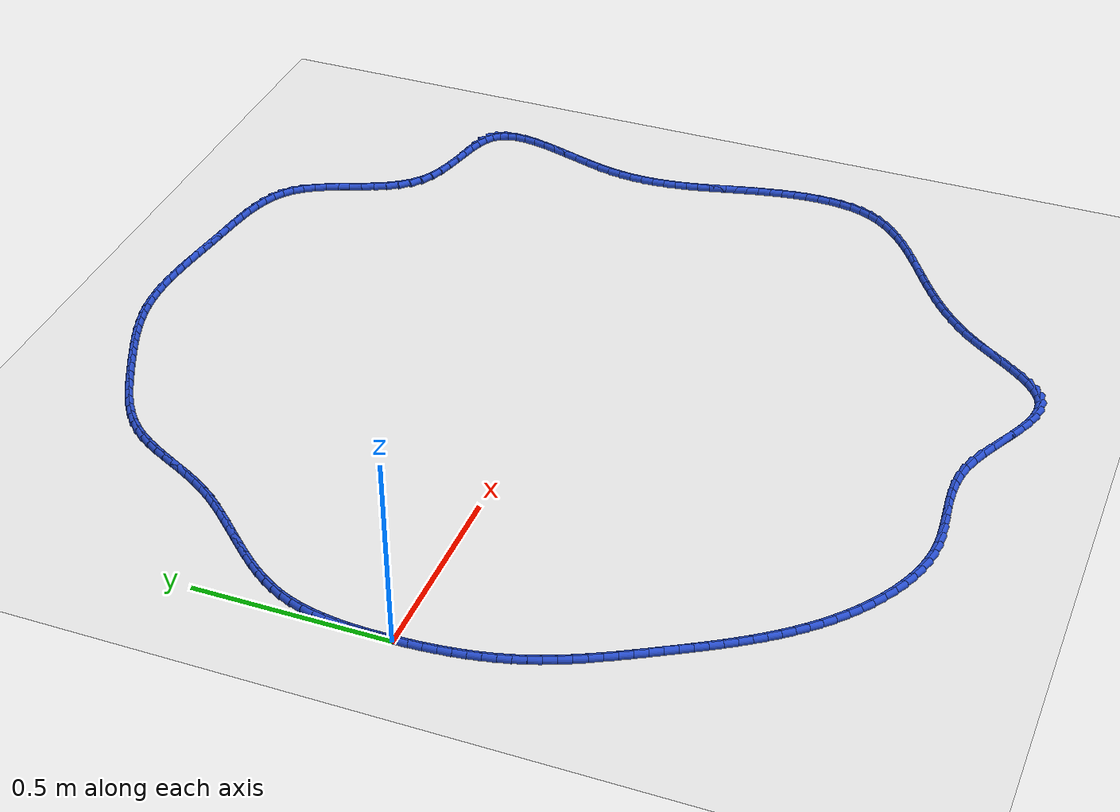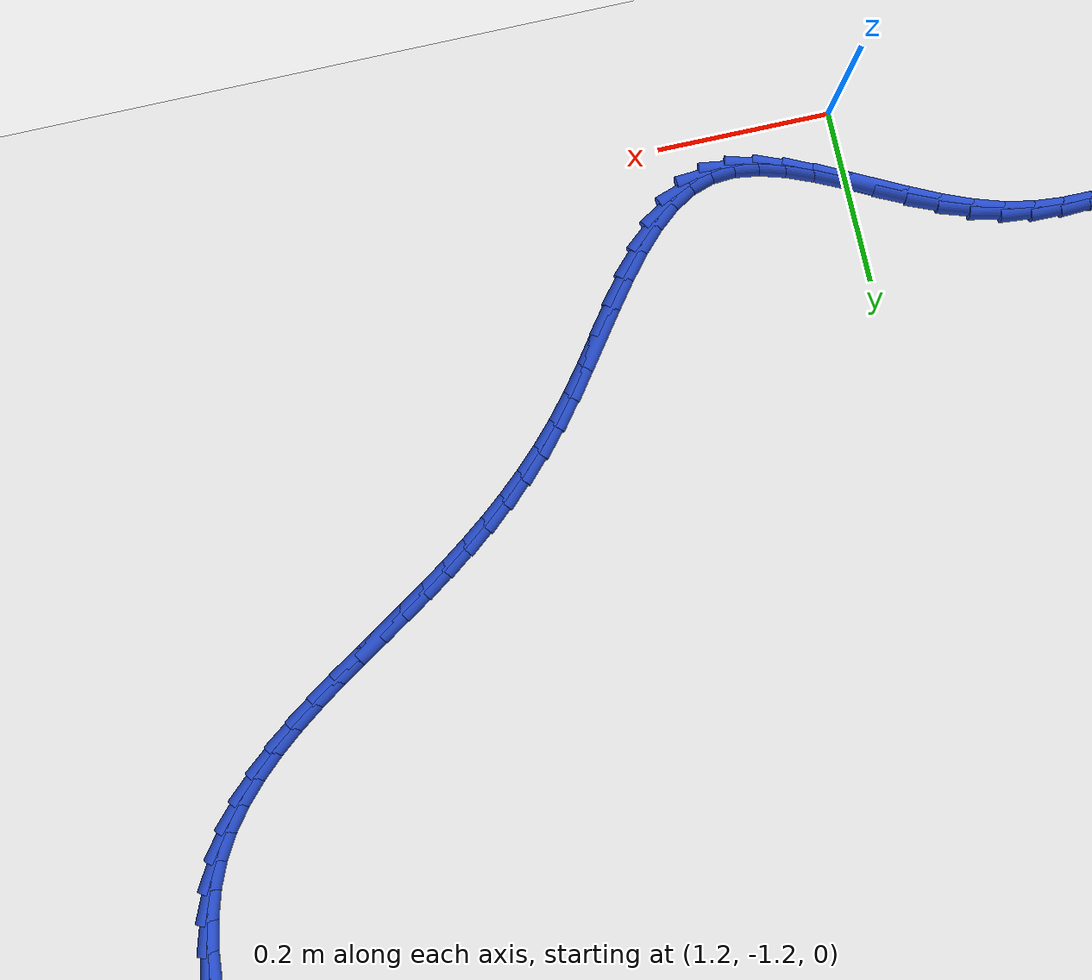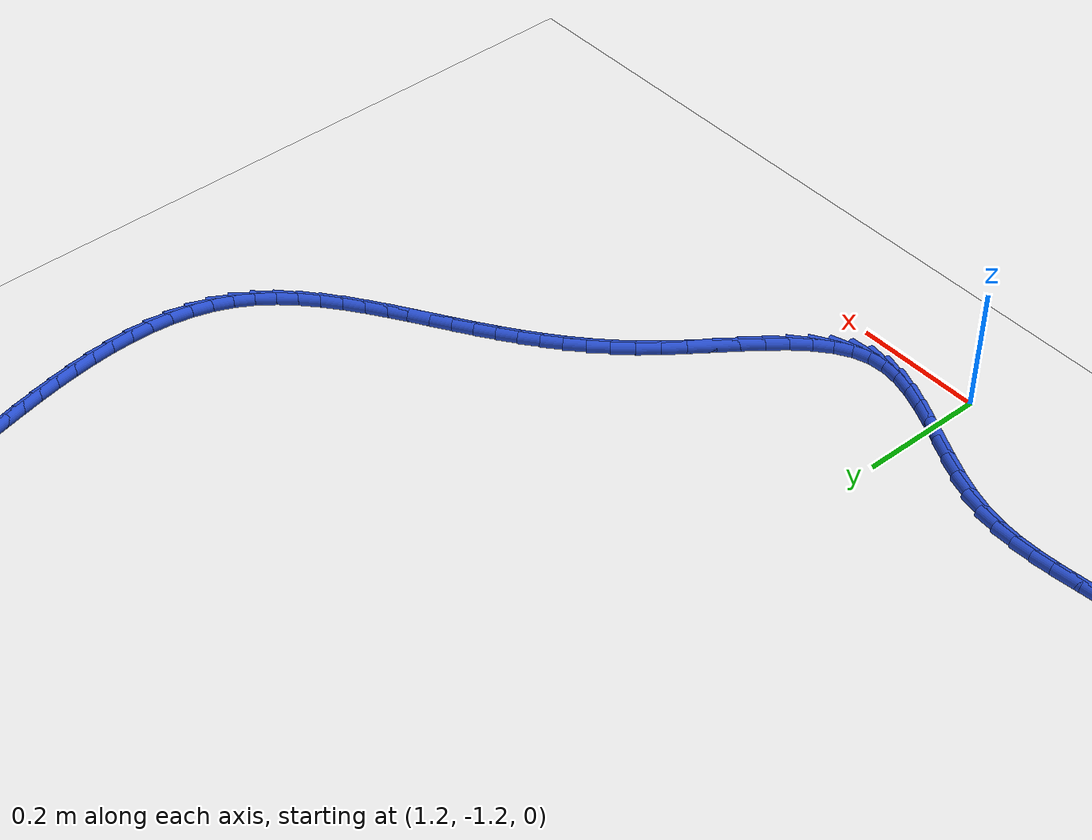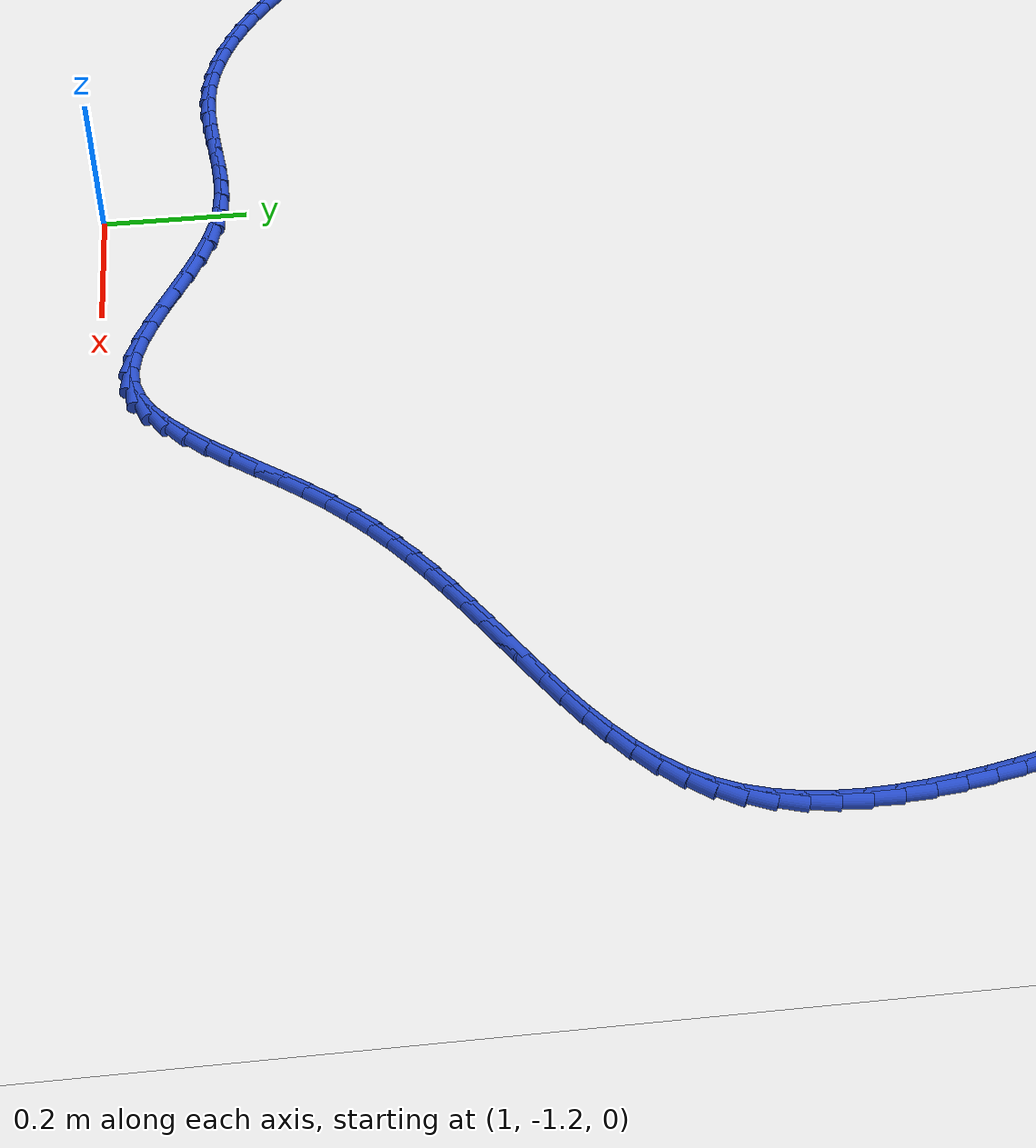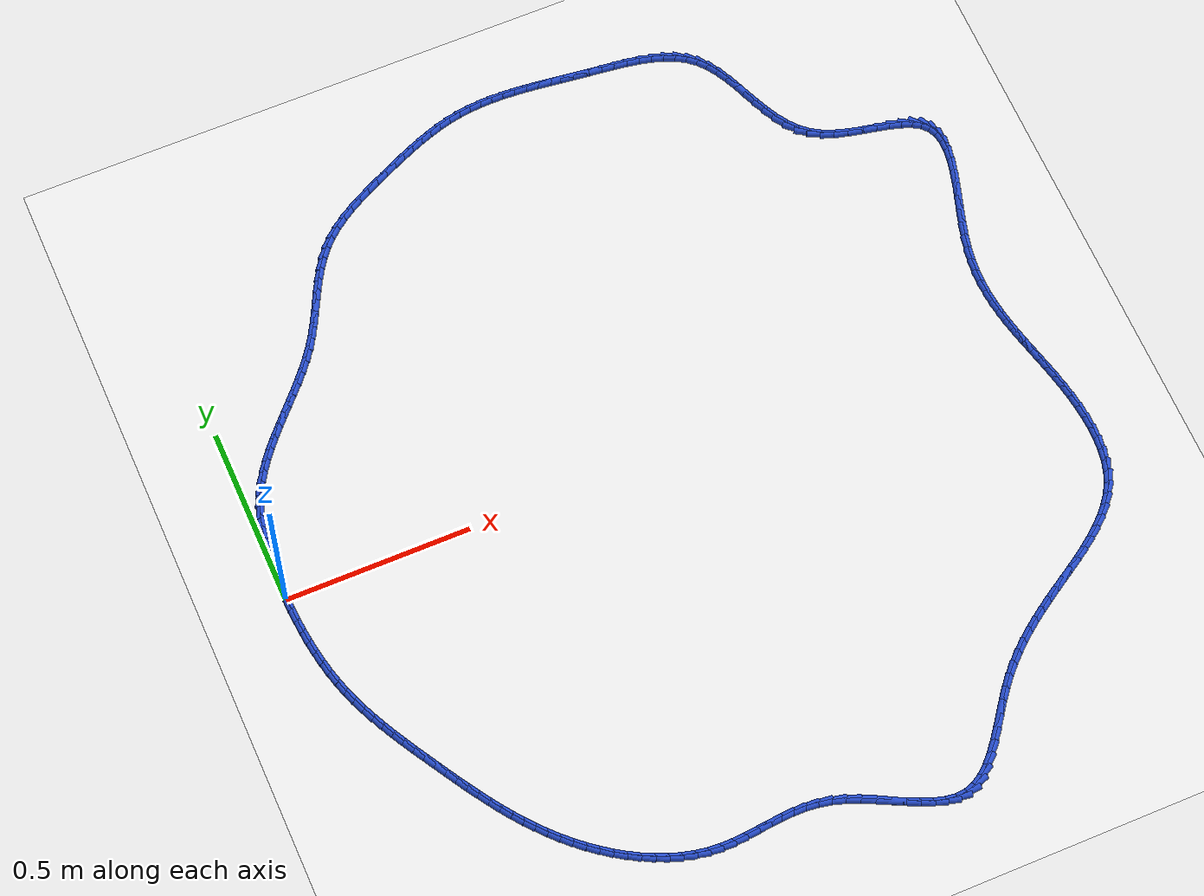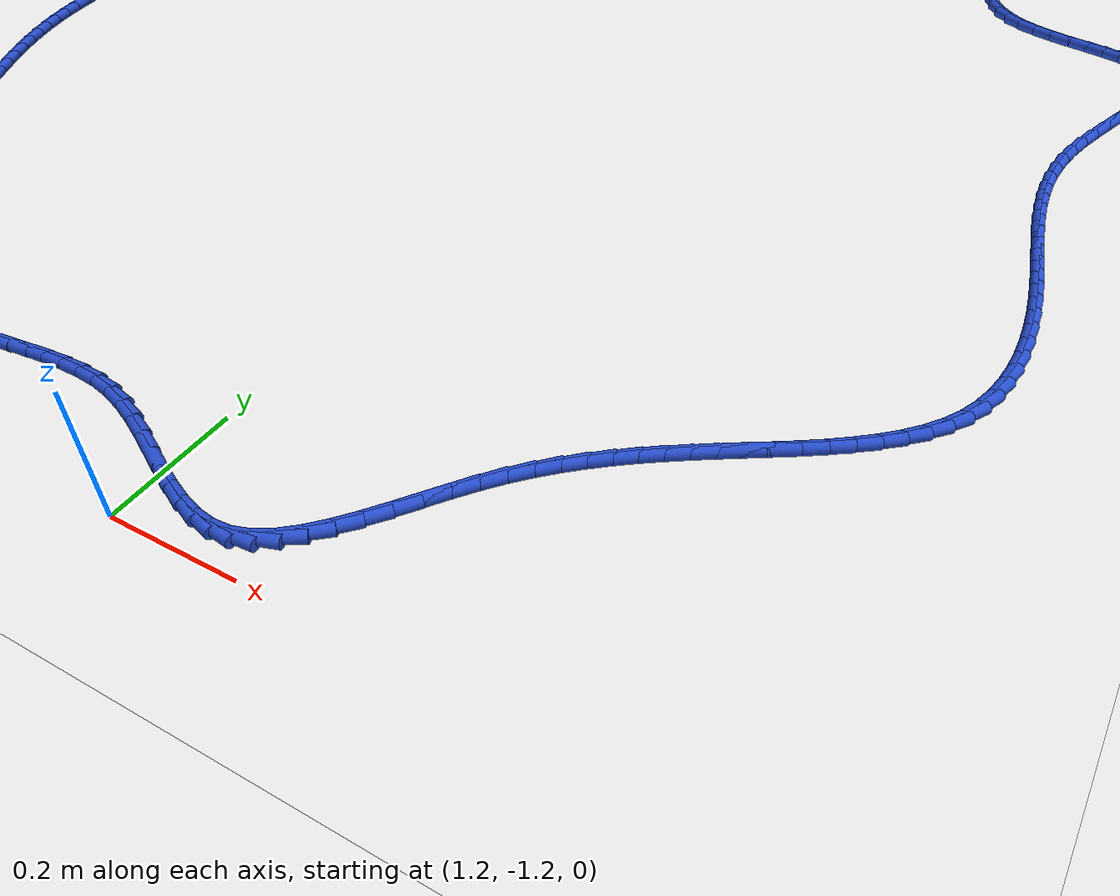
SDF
<sdf version="1.6">
 <world name="default">
  <light name="sun" type="directional">
   <pose>0 0 10 0 -0 0</pose>
   <diffuse>0.8 0.8 0.8 1</diffuse>
   <specular>0.2 0.2 0.2 1</specular>
   <attenuation>
    <range>1000</range>
    <constant>0.9</constant>
    <linear>0.01</linear>
    <quadratic>0.001</quadratic>
   </attenuation>
   <direction>-0.5 0.1 -0.9</direction>
  </light>
  <model name="ground_plane">
   <static>1</static>
   <link name="link">
    <collision name="collision">
     <geometry><plane><normal>0 0 1</normal><size>100 100</size></plane></geometry>
     <surface><friction><ode><mu>100</mu><mu2>50</mu2></ode></friction></surface>
    </collision>
    <visual name="visual">
     <cast_shadows>0</cast_shadows>
     <geometry><plane><normal>0 0 1</normal><size>100 100</size></plane></geometry>
     <material>
      <script><uri>file://media/materials/scripts/gazebo.material</uri><name>Gazebo/WhiteGlow</name></script>
     </material>
    </visual>
   </link>
  </model>
  <gravity>0 0 -9.8</gravity>
  <magnetic_field>6e-06 2.3e-05 -4.2e-05</magnetic_field>
  <atmosphere type="adiabatic"/>
  <physics name="default_physics" default="0" type="ode">
   <max_step_size>0.001</max_step_size>
   <real_time_factor>1</real_time_factor>
   <real_time_update_rate>1000</real_time_update_rate>
  </physics>
  <scene><ambient>0.4 0.4 0.4 1</ambient><background>0.7 0.7 0.7 1</background><shadows>1</shadows></scene>
  <spherical_coordinates>
   <surface_model>EARTH_WGS84</surface_model>
   <latitude_deg>0</latitude_deg>
   <longitude_deg>0</longitude_deg>
   <elevation>0</elevation>
   <heading_deg>0</heading_deg>
  </spherical_coordinates>
  <model name="line">
   <link name="link_0">
    <pose>3.469446951953614e-18 -6.938893903907228e-18 0.01 0 1.57 -1.5600007754396892</pose>
    <collision name="collision">
     <geometry><cylinder><radius>0.01</radius><length>0.08</length></cylinder></geometry>
    </collision>
    <visual name="visual">
     <material>
      <script><name>Gazebo/Blue</name><uri>file://media/materials/scripts/gazebo.material</uri></script>
     </material>
     <geometry><cylinder><radius>0.01</radius><length>0.08</length></cylinder></geometry>
    </visual>
   </link>
   <link name="link_1">
    <pose>-0.0003693970486968015 0.03421619573689655 0.01 0 1.57 1.5554484758334015</pose>
    <collision name="collision">
     <geometry><cylinder><radius>0.01</radius><length>0.08</length></cylinder></geometry>
    </collision>
    <visual name="visual">
     <material>
      <script><name>Gazebo/Blue</name><uri>file://media/materials/scripts/gazebo.material</uri></script>
     </material>
     <geometry><cylinder><radius>0.01</radius><length>0.08</length></cylinder></geometry>
    </visual>
   </link>
   <link name="link_2">
    <pose>0.00015649383802368924 0.0684782950397433 0.01 0 1.57 1.5236202056912242</pose>
    <collision name="collision">
     <geometry><cylinder><radius>0.01</radius><length>0.08</length></cylinder></geometry>
    </collision>
    <visual name="visual">
     <material>
      <script><name>Gazebo/Blue</name><uri>file://media/materials/scripts/gazebo.material</uri></script>
     </material>
     <geometry><cylinder><radius>0.01</radius><length>0.08</length></cylinder></geometry>
    </visual>
   </link>
   <link name="link_3">
    <pose>0.0017685057791543288 0.10262302409657 0.01 0 1.57 1.4856917676888064</pose>
    <collision name="collision">
     <geometry><cylinder><radius>0.01</radius><length>0.08</length></cylinder></geometry>
    </collision>
    <visual name="visual">
     <material>
      <script><name>Gazebo/Blue</name><uri>file://media/materials/scripts/gazebo.material</uri></script>
     </material>
     <geometry><cylinder><radius>0.01</radius><length>0.08</length></cylinder></geometry>
    </visual>
   </link>
   <link name="link_4">
    <pose>0.004657471893687967 0.13648710909540637 0.01 0 1.57 1.4411643673800123</pose>
    <collision name="collision">
     <geometry><cylinder><radius>0.01</radius><length>0.08</length></cylinder></geometry>
    </collision>
    <visual name="visual">
     <material>
      <script><name>Gazebo/Blue</name><uri>file://media/materials/scripts/gazebo.material</uri></script>
     </material>
     <geometry><cylinder><radius>0.01</radius><length>0.08</length></cylinder></geometry>
    </visual>
   </link>
   <link name="link_5">
    <pose>0.009014225300617455 0.16990727622428223 0.01 0 1.57 1.3894865284816937</pose>
    <collision name="collision">
     <geometry><cylinder><radius>0.01</radius><length>0.08</length></cylinder></geometry>
    </collision>
    <visual name="visual">
     <material>
      <script><name>Gazebo/Blue</name><uri>file://media/materials/scripts/gazebo.material</uri></script>
     </material>
     <geometry><cylinder><radius>0.01</radius><length>0.08</length></cylinder></geometry>
    </visual>
   </link>
   <link name="link_6">
    <pose>0.015029599118935645 0.20272025167122742 0.01 0 1.57 1.330104777681257</pose>
    <collision name="collision">
     <geometry><cylinder><radius>0.01</radius><length>0.08</length></cylinder></geometry>
    </collision>
    <visual name="visual">
     <material>
      <script><name>Gazebo/Blue</name><uri>file://media/materials/scripts/gazebo.material</uri></script>
     </material>
     <geometry><cylinder><radius>0.01</radius><length>0.08</length></cylinder></geometry>
    </visual>
   </link>
   <link name="link_7">
    <pose>0.022894426467635395 0.2347627616242717 0.01 0 1.57 1.262543057963074</pose>
    <collision name="collision">
     <geometry><cylinder><radius>0.01</radius><length>0.08</length></cylinder></geometry>
    </collision>
    <visual name="visual">
     <material>
      <script><name>Gazebo/Blue</name><uri>file://media/materials/scripts/gazebo.material</uri></script>
     </material>
     <geometry><cylinder><radius>0.01</radius><length>0.08</length></cylinder></geometry>
    </visual>
   </link>
   <link name="link_8">
    <pose>0.03279954046570955 0.26587153227144483 0.01 0 1.57 1.1865176995141657</pose>
    <collision name="collision">
     <geometry><cylinder><radius>0.01</radius><length>0.08</length></cylinder></geometry>
    </collision>
    <visual name="visual">
     <material>
      <script><name>Gazebo/Blue</name><uri>file://media/materials/scripts/gazebo.material</uri></script>
     </material>
     <geometry><cylinder><radius>0.01</radius><length>0.08</length></cylinder></geometry>
    </visual>
   </link>
   <link name="link_9">
    <pose>0.04493576959993535 0.295883292981483 0.01 0 1.57 1.1055190774696992</pose>
    <collision name="collision">
     <geometry><cylinder><radius>0.01</radius><length>0.08</length></cylinder></geometry>
    </collision>
    <visual name="visual">
     <material>
      <script><name>Gazebo/Blue</name><uri>file://media/materials/scripts/gazebo.material</uri></script>
     </material>
     <geometry><cylinder><radius>0.01</radius><length>0.08</length></cylinder></geometry>
    </visual>
   </link>
   <link name="link_10">
    <pose>0.05940186649474283 0.32469799692529017 0.01 0 1.57 1.0324860794601485</pose>
    <collision name="collision">
     <geometry><cylinder><radius>0.01</radius><length>0.08</length></cylinder></geometry>
    </collision>
    <visual name="visual">
     <material>
      <script><name>Gazebo/Blue</name><uri>file://media/materials/scripts/gazebo.material</uri></script>
     </material>
     <geometry><cylinder><radius>0.01</radius><length>0.08</length></cylinder></geometry>
    </visual>
   </link>
   <link name="link_11">
    <pose>0.07596822443103515 0.352441064900637 0.01 0 1.57 0.970878481248477</pose>
    <collision name="collision">
     <geometry><cylinder><radius>0.01</radius><length>0.08</length></cylinder></geometry>
    </collision>
    <visual name="visual">
     <material>
      <script><name>Gazebo/Blue</name><uri>file://media/materials/scripts/gazebo.material</uri></script>
     </material>
     <geometry><cylinder><radius>0.01</radius><length>0.08</length></cylinder></geometry>
    </visual>
   </link>
   <link name="link_12">
    <pose>0.09433207065185885 0.3792881570946944 0.01 0 1.57 0.9208722245230099</pose>
    <collision name="collision">
     <geometry><cylinder><radius>0.01</radius><length>0.08</length></cylinder></geometry>
    </collision>
    <visual name="visual">
     <material>
      <script><name>Gazebo/Blue</name><uri>file://media/materials/scripts/gazebo.material</uri></script>
     </material>
     <geometry><cylinder><radius>0.01</radius><length>0.08</length></cylinder></geometry>
    </visual>
   </link>
   <link name="link_13">
    <pose>0.11419063240026037 0.4054149336946331 0.01 0 1.57 0.8822709498419058</pose>
    <collision name="collision">
     <geometry><cylinder><radius>0.01</radius><length>0.08</length></cylinder></geometry>
    </collision>
    <visual name="visual">
     <material>
      <script><name>Gazebo/Blue</name><uri>file://media/materials/scripts/gazebo.material</uri></script>
     </material>
     <geometry><cylinder><radius>0.01</radius><length>0.08</length></cylinder></geometry>
    </visual>
   </link>
   <link name="link_14">
    <pose>0.1352411369192864 0.4309970548876248 0.01 0 1.57 0.8547091655558868</pose>
    <collision name="collision">
     <geometry><cylinder><radius>0.01</radius><length>0.08</length></cylinder></geometry>
    </collision>
    <visual name="visual">
     <material>
      <script><name>Gazebo/Blue</name><uri>file://media/materials/scripts/gazebo.material</uri></script>
     </material>
     <geometry><cylinder><radius>0.01</radius><length>0.08</length></cylinder></geometry>
    </visual>
   </link>
   <link name="link_15">
    <pose>0.15718081145198323 0.45621018086084 0.01 0 1.57 0.8377988591644435</pose>
    <collision name="collision">
     <geometry><cylinder><radius>0.01</radius><length>0.08</length></cylinder></geometry>
    </collision>
    <visual name="visual">
     <material>
      <script><name>Gazebo/Blue</name><uri>file://media/materials/scripts/gazebo.material</uri></script>
     </material>
     <geometry><cylinder><radius>0.01</radius><length>0.08</length></cylinder></geometry>
    </visual>
   </link>
   <link name="link_16">
    <pose>0.17970688324139752 0.48122997180145005 0.01 0 1.57 0.8312212553598523</pose>
    <collision name="collision">
     <geometry><cylinder><radius>0.01</radius><length>0.08</length></cylinder></geometry>
    </collision>
    <visual name="visual">
     <material>
      <script><name>Gazebo/Blue</name><uri>file://media/materials/scripts/gazebo.material</uri></script>
     </material>
     <geometry><cylinder><radius>0.01</radius><length>0.08</length></cylinder></geometry>
    </visual>
   </link>
   <link name="link_17">
    <pose>0.20251657953057575 0.5062320878966257 0.01 0 1.57 0.834774500175812</pose>
    <collision name="collision">
     <geometry><cylinder><radius>0.01</radius><length>0.08</length></cylinder></geometry>
    </collision>
    <visual name="visual">
     <material>
      <script><name>Gazebo/Blue</name><uri>file://media/materials/scripts/gazebo.material</uri></script>
     </material>
     <geometry><cylinder><radius>0.01</radius><length>0.08</length></cylinder></geometry>
    </visual>
   </link>
   <link name="link_18">
    <pose>0.22530712756256438 0.5313921893335383 0.01 0 1.57 0.8483874977379311</pose>
    <collision name="collision">
     <geometry><cylinder><radius>0.01</radius><length>0.08</length></cylinder></geometry>
    </collision>
    <visual name="visual">
     <material>
      <script><name>Gazebo/Blue</name><uri>file://media/materials/scripts/gazebo.material</uri></script>
     </material>
     <geometry><cylinder><radius>0.01</radius><length>0.08</length></cylinder></geometry>
    </visual>
   </link>
   <link name="link_19">
    <pose>0.24777575458041012 0.5568859362993587 0.01 0 1.57 0.8721056354768278</pose>
    <collision name="collision">
     <geometry><cylinder><radius>0.01</radius><length>0.08</length></cylinder></geometry>
    </collision>
    <visual name="visual">
     <material>
      <script><name>Gazebo/Blue</name><uri>file://media/materials/scripts/gazebo.material</uri></script>
     </material>
     <geometry><cylinder><radius>0.01</radius><length>0.08</length></cylinder></geometry>
    </visual>
   </link>
   <link name="link_20">
    <pose>0.2696196878271593 0.582888988981258 0.01 0 1.57 0.9060489771773454</pose>
    <collision name="collision">
     <geometry><cylinder><radius>0.01</radius><length>0.08</length></cylinder></geometry>
    </collision>
    <visual name="visual">
     <material>
      <script><name>Gazebo/Blue</name><uri>file://media/materials/scripts/gazebo.material</uri></script>
     </material>
     <geometry><cylinder><radius>0.01</radius><length>0.08</length></cylinder></geometry>
    </visual>
   </link>
   <link name="link_21">
    <pose>0.29053615454585835 0.6095770075664071 0.01 0 1.57 0.9503395818592171</pose>
    <collision name="collision">
     <geometry><cylinder><radius>0.01</radius><length>0.08</length></cylinder></geometry>
    </collision>
    <visual name="visual">
     <material>
      <script><name>Gazebo/Blue</name><uri>file://media/materials/scripts/gazebo.material</uri></script>
     </material>
     <geometry><cylinder><radius>0.01</radius><length>0.08</length></cylinder></geometry>
    </visual>
   </link>
   <link name="link_22">
    <pose>0.3102223819795541 0.6371256522419773 0.01 0 1.57 1.004442072257231</pose>
    <collision name="collision">
     <geometry><cylinder><radius>0.01</radius><length>0.08</length></cylinder></geometry>
    </collision>
    <visual name="visual">
     <material>
      <script><name>Gazebo/Blue</name><uri>file://media/materials/scripts/gazebo.material</uri></script>
     </material>
     <geometry><cylinder><radius>0.01</radius><length>0.08</length></cylinder></geometry>
    </visual>
   </link>
   <link name="link_23">
    <pose>0.3283908379875737 0.6656997322464746 0.01 0 1.57 1.0549218515984744</pose>
    <collision name="collision">
     <geometry><cylinder><radius>0.01</radius><length>0.08</length></cylinder></geometry>
    </collision>
    <visual name="visual">
     <material>
      <script><name>Gazebo/Blue</name><uri>file://media/materials/scripts/gazebo.material</uri></script>
     </material>
     <geometry><cylinder><radius>0.01</radius><length>0.08</length></cylinder></geometry>
    </visual>
   </link>
   <link name="link_24">
    <pose>0.34512164507003096 0.6952022956428747 0.01 0 1.57 1.088226265606407</pose>
    <collision name="collision">
     <geometry><cylinder><radius>0.01</radius><length>0.08</length></cylinder></geometry>
    </collision>
    <visual name="visual">
     <material>
      <script><name>Gazebo/Blue</name><uri>file://media/materials/scripts/gazebo.material</uri></script>
     </material>
     <geometry><cylinder><radius>0.01</radius><length>0.08</length></cylinder></geometry>
    </visual>
   </link>
   <link name="link_25">
    <pose>0.3608723510250425 0.7252676728479699 0.01 0 1.57 1.103974739045045</pose>
    <collision name="collision">
     <geometry><cylinder><radius>0.01</radius><length>0.08</length></cylinder></geometry>
    </collision>
    <visual name="visual">
     <material>
      <script><name>Gazebo/Blue</name><uri>file://media/materials/scripts/gazebo.material</uri></script>
     </material>
     <geometry><cylinder><radius>0.01</radius><length>0.08</length></cylinder></geometry>
    </visual>
   </link>
   <link name="link_26">
    <pose>0.37611769881988083 0.755517951735708 0.01 0 1.57 1.1022078265134752</pose>
    <collision name="collision">
     <geometry><cylinder><radius>0.01</radius><length>0.08</length></cylinder></geometry>
    </collision>
    <visual name="visual">
     <material>
      <script><name>Gazebo/Blue</name><uri>file://media/materials/scripts/gazebo.material</uri></script>
     </material>
     <geometry><cylinder><radius>0.01</radius><length>0.08</length></cylinder></geometry>
    </visual>
   </link>
   <link name="link_27">
    <pose>0.39133243142181834 0.7855752201800373 0.01 0 1.57 1.0826147590760773</pose>
    <collision name="collision">
     <geometry><cylinder><radius>0.01</radius><length>0.08</length></cylinder></geometry>
    </collision>
    <visual name="visual">
     <material>
      <script><name>Gazebo/Blue</name><uri>file://media/materials/scripts/gazebo.material</uri></script>
     </material>
     <geometry><cylinder><radius>0.01</radius><length>0.08</length></cylinder></geometry>
    </visual>
   </link>
   <link name="link_28">
    <pose>0.4069912917981277 0.8150615660549061 0.01 0 1.57 1.044531724250901</pose>
    <collision name="collision">
     <geometry><cylinder><radius>0.01</radius><length>0.08</length></cylinder></geometry>
    </collision>
    <visual name="visual">
     <material>
      <script><name>Gazebo/Blue</name><uri>file://media/materials/scripts/gazebo.material</uri></script>
     </material>
     <geometry><cylinder><radius>0.01</radius><length>0.08</length></cylinder></geometry>
    </visual>
   </link>
   <link name="link_29">
    <pose>0.4235690229160811 0.843599077234262 0.01 0 1.57 0.9871100418344582</pose>
    <collision name="collision">
     <geometry><cylinder><radius>0.01</radius><length>0.08</length></cylinder></geometry>
    </collision>
    <visual name="visual">
     <material>
      <script><name>Gazebo/Blue</name><uri>file://media/materials/scripts/gazebo.material</uri></script>
     </material>
     <geometry><cylinder><radius>0.01</radius><length>0.08</length></cylinder></geometry>
    </visual>
   </link>
   <link name="link_30">
    <pose>0.4415403677429517 0.8708098415920539 0.01 0 1.57 0.9097135967163266</pose>
    <collision name="collision">
     <geometry><cylinder><radius>0.01</radius><length>0.08</length></cylinder></geometry>
    </collision>
    <visual name="visual">
     <material>
      <script><name>Gazebo/Blue</name><uri>file://media/materials/scripts/gazebo.material</uri></script>
     </material>
     <geometry><cylinder><radius>0.01</radius><length>0.08</length></cylinder></geometry>
    </visual>
   </link>
   <link name="link_31">
    <pose>0.46138006924601116 0.8963159470022288 0.01 0 1.57 0.8147684112072956</pose>
    <collision name="collision">
     <geometry><cylinder><radius>0.01</radius><length>0.08</length></cylinder></geometry>
    </collision>
    <visual name="visual">
     <material>
      <script><name>Gazebo/Blue</name><uri>file://media/materials/scripts/gazebo.material</uri></script>
     </material>
     <geometry><cylinder><radius>0.01</radius><length>0.08</length></cylinder></geometry>
    </visual>
   </link>
   <link name="link_32">
    <pose>0.48350801046168673 0.9197834220813806 0.01 0 1.57 0.7229272235167186</pose>
    <collision name="collision">
     <geometry><cylinder><radius>0.01</radius><length>0.08</length></cylinder></geometry>
    </collision>
    <visual name="visual">
     <material>
      <script><name>Gazebo/Blue</name><uri>file://media/materials/scripts/gazebo.material</uri></script>
     </material>
     <geometry><cylinder><radius>0.01</radius><length>0.08</length></cylinder></geometry>
    </visual>
   </link>
   <link name="link_33">
    <pose>0.5078586970794982 0.9412670644576057 0.01 0 1.57 0.645120619608636</pose>
    <collision name="collision">
     <geometry><cylinder><radius>0.01</radius><length>0.08</length></cylinder></geometry>
    </collision>
    <visual name="visual">
     <material>
      <script><name>Gazebo/Blue</name><uri>file://media/materials/scripts/gazebo.material</uri></script>
     </material>
     <geometry><cylinder><radius>0.01</radius><length>0.08</length></cylinder></geometry>
    </visual>
   </link>
   <link name="link_34">
    <pose>0.5341133315458985 0.9610245581360544 0.01 0 1.57 0.5813178647892413</pose>
    <collision name="collision">
     <geometry><cylinder><radius>0.01</radius><length>0.08</length></cylinder></geometry>
    </collision>
    <visual name="visual">
     <material>
      <script><name>Gazebo/Blue</name><uri>file://media/materials/scripts/gazebo.material</uri></script>
     </material>
     <geometry><cylinder><radius>0.01</radius><length>0.08</length></cylinder></geometry>
    </visual>
   </link>
   <link name="link_35">
    <pose>0.5619509197238134 0.9793153465027213 0.01 0 1.57 0.5308592978552239</pose>
    <collision name="collision">
     <geometry><cylinder><radius>0.01</radius><length>0.08</length></cylinder></geometry>
    </collision>
    <visual name="visual">
     <material>
      <script><name>Gazebo/Blue</name><uri>file://media/materials/scripts/gazebo.material</uri></script>
     </material>
     <geometry><cylinder><radius>0.01</radius><length>0.08</length></cylinder></geometry>
    </visual>
   </link>
   <link name="link_36">
    <pose>0.5910504674761693 0.9963988729436012 0.01 0 1.57 0.49290976307720036</pose>
    <collision name="collision">
     <geometry><cylinder><radius>0.01</radius><length>0.08</length></cylinder></geometry>
    </collision>
    <visual name="visual">
     <material>
      <script><name>Gazebo/Blue</name><uri>file://media/materials/scripts/gazebo.material</uri></script>
     </material>
     <geometry><cylinder><radius>0.01</radius><length>0.08</length></cylinder></geometry>
    </visual>
   </link>
   <link name="link_37">
    <pose>0.6210909806658925 1.0125345808446884 0.01 0 1.57 0.46669809042227167</pose>
    <collision name="collision">
     <geometry><cylinder><radius>0.01</radius><length>0.08</length></cylinder></geometry>
    </collision>
    <visual name="visual">
     <material>
      <script><name>Gazebo/Blue</name><uri>file://media/materials/scripts/gazebo.material</uri></script>
     </material>
     <geometry><cylinder><radius>0.01</radius><length>0.08</length></cylinder></geometry>
    </visual>
   </link>
   <link name="link_38">
    <pose>0.6517514651559089 1.0279819135919779 0.01 0 1.57 0.451655828998194</pose>
    <collision name="collision">
     <geometry><cylinder><radius>0.01</radius><length>0.08</length></cylinder></geometry>
    </collision>
    <visual name="visual">
     <material>
      <script><name>Gazebo/Blue</name><uri>file://media/materials/scripts/gazebo.material</uri></script>
     </material>
     <geometry><cylinder><radius>0.01</radius><length>0.08</length></cylinder></geometry>
    </visual>
   </link>
   <link name="link_39">
    <pose>0.6827109268091447 1.0430003145714644 0.01 0 1.57 0.4446764041633225</pose>
    <collision name="collision">
     <geometry><cylinder><radius>0.01</radius><length>0.08</length></cylinder></geometry>
    </collision>
    <visual name="visual">
     <material>
      <script><name>Gazebo/Blue</name><uri>file://media/materials/scripts/gazebo.material</uri></script>
     </material>
     <geometry><cylinder><radius>0.01</radius><length>0.08</length></cylinder></geometry>
    </visual>
   </link>
   <link name="link_40">
    <pose>0.7137035463838828 1.057768484678155 0.01 0 1.57 0.43388995854553764</pose>
    <collision name="collision">
     <geometry><cylinder><radius>0.01</radius><length>0.08</length></cylinder></geometry>
    </collision>
    <visual name="visual">
     <material>
      <script><name>Gazebo/Blue</name><uri>file://media/materials/scripts/gazebo.material</uri></script>
     </material>
     <geometry><cylinder><radius>0.01</radius><length>0.08</length></cylinder></geometry>
    </visual>
   </link>
   <link name="link_41">
    <pose>0.7446941517880932 1.0721275976530067 0.01 0 1.57 0.41604636014040325</pose>
    <collision name="collision">
     <geometry><cylinder><radius>0.01</radius><length>0.08</length></cylinder></geometry>
    </collision>
    <visual name="visual">
     <material>
      <script><name>Gazebo/Blue</name><uri>file://media/materials/scripts/gazebo.material</uri></script>
     </material>
     <geometry><cylinder><radius>0.01</radius><length>0.08</length></cylinder></geometry>
    </visual>
   </link>
   <link name="link_42">
    <pose>0.7757078306839538 1.0858306436051008 0.01 0 1.57 0.39087675499155444</pose>
    <collision name="collision">
     <geometry><cylinder><radius>0.01</radius><length>0.08</length></cylinder></geometry>
    </collision>
    <visual name="visual">
     <material>
      <script><name>Gazebo/Blue</name><uri>file://media/materials/scripts/gazebo.material</uri></script>
     </material>
     <geometry><cylinder><radius>0.01</radius><length>0.08</length></cylinder></geometry>
    </visual>
   </link>
   <link name="link_43">
    <pose>0.8067696709166298 1.0986306123757341 0.01 0 1.57 0.3580446325179453</pose>
    <collision name="collision">
     <geometry><cylinder><radius>0.01</radius><length>0.08</length></cylinder></geometry>
    </collision>
    <visual name="visual">
     <material>
      <script><name>Gazebo/Blue</name><uri>file://media/materials/scripts/gazebo.material</uri></script>
     </material>
     <geometry><cylinder><radius>0.01</radius><length>0.08</length></cylinder></geometry>
    </visual>
   </link>
   <link name="link_44">
    <pose>0.8379047603312868 1.1102804938062052 0.01 0 1.57 0.3171804982124579</pose>
    <collision name="collision">
     <geometry><cylinder><radius>0.01</radius><length>0.08</length></cylinder></geometry>
    </collision>
    <visual name="visual">
     <material>
      <script><name>Gazebo/Blue</name><uri>file://media/materials/scripts/gazebo.material</uri></script>
     </material>
     <geometry><cylinder><radius>0.01</radius><length>0.08</length></cylinder></geometry>
    </visual>
   </link>
   <link name="link_45">
    <pose>0.8691381867730895 1.1205332777378114 0.01 0 1.57 0.2679375033169996</pose>
    <collision name="collision">
     <geometry><cylinder><radius>0.01</radius><length>0.08</length></cylinder></geometry>
    </collision>
    <visual name="visual">
     <material>
      <script><name>Gazebo/Blue</name><uri>file://media/materials/scripts/gazebo.material</uri></script>
     </material>
     <geometry><cylinder><radius>0.01</radius><length>0.08</length></cylinder></geometry>
    </visual>
   </link>
   <link name="link_46">
    <pose>0.9004950380872039 1.129141954011851 0.01 0 1.57 0.21007408411947323</pose>
    <collision name="collision">
     <geometry><cylinder><radius>0.01</radius><length>0.08</length></cylinder></geometry>
    </collision>
    <visual name="visual">
     <material>
      <script><name>Gazebo/Blue</name><uri>file://media/materials/scripts/gazebo.material</uri></script>
     </material>
     <geometry><cylinder><radius>0.01</radius><length>0.08</length></cylinder></geometry>
    </visual>
   </link>
   <link name="link_47">
    <pose>0.9320004023280446 1.1358595244780794 0.01 0 1.57 0.14637469811863807</pose>
    <collision name="collision">
     <geometry><cylinder><radius>0.01</radius><length>0.08</length></cylinder></geometry>
    </collision>
    <visual name="visual">
     <material>
      <script><name>Gazebo/Blue</name><uri>file://media/materials/scripts/gazebo.material</uri></script>
     </material>
     <geometry><cylinder><radius>0.01</radius><length>0.08</length></cylinder></geometry>
    </visual>
   </link>
   <link name="link_48">
    <pose>0.9636809562007738 1.1405301607179192 0.01 0 1.57 0.08691518619179942</pose>
    <collision name="collision">
     <geometry><cylinder><radius>0.01</radius><length>0.08</length></cylinder></geometry>
    </collision>
    <visual name="visual">
     <material>
      <script><name>Gazebo/Blue</name><uri>file://media/materials/scripts/gazebo.material</uri></script>
     </material>
     <geometry><cylinder><radius>0.01</radius><length>0.08</length></cylinder></geometry>
    </visual>
   </link>
   <link name="link_49">
    <pose>0.9955687897841753 1.1433086978248095 0.01 0 1.57 0.03445390394666366</pose>
    <collision name="collision">
     <geometry><cylinder><radius>0.01</radius><length>0.08</length></cylinder></geometry>
    </collision>
    <visual name="visual">
     <material>
      <script><name>Gazebo/Blue</name><uri>file://media/materials/scripts/gazebo.material</uri></script>
     </material>
     <geometry><cylinder><radius>0.01</radius><length>0.08</length></cylinder></geometry>
    </visual>
   </link>
   <link name="link_50">
    <pose>1.027697145179128 1.1444160833121484 0.01 0 1.57 -0.010579734764060546</pose>
    <collision name="collision">
     <geometry><cylinder><radius>0.01</radius><length>0.08</length></cylinder></geometry>
    </collision>
    <visual name="visual">
     <material>
      <script><name>Gazebo/Blue</name><uri>file://media/materials/scripts/gazebo.material</uri></script>
     </material>
     <geometry><cylinder><radius>0.01</radius><length>0.08</length></cylinder></geometry>
    </visual>
   </link>
   <link name="link_51">
    <pose>1.0600992644865117 1.1440732646933347 0.01 0 1.57 -0.04802532571994697</pose>
    <collision name="collision">
     <geometry><cylinder><radius>0.01</radius><length>0.08</length></cylinder></geometry>
    </collision>
    <visual name="visual">
     <material>
      <script><name>Gazebo/Blue</name><uri>file://media/materials/scripts/gazebo.material</uri></script>
     </material>
     <geometry><cylinder><radius>0.01</radius><length>0.08</length></cylinder></geometry>
    </visual>
   </link>
   <link name="link_52">
    <pose>1.0928083898072063 1.1425011894817672 0.01 0 1.57 -0.07791857481641183</pose>
    <collision name="collision">
     <geometry><cylinder><radius>0.01</radius><length>0.08</length></cylinder></geometry>
    </collision>
    <visual name="visual">
     <material>
      <script><name>Gazebo/Blue</name><uri>file://media/materials/scripts/gazebo.material</uri></script>
     </material>
     <geometry><cylinder><radius>0.01</radius><length>0.08</length></cylinder></geometry>
    </visual>
   </link>
   <link name="link_53">
    <pose>1.1258577632420914 1.139920805190844 0.01 0 1.57 -0.10042279229799518</pose>
    <collision name="collision">
     <geometry><cylinder><radius>0.01</radius><length>0.08</length></cylinder></geometry>
    </collision>
    <visual name="visual">
     <material>
      <script><name>Gazebo/Blue</name><uri>file://media/materials/scripts/gazebo.material</uri></script>
     </material>
     <geometry><cylinder><radius>0.01</radius><length>0.08</length></cylinder></geometry>
    </visual>
   </link>
   <link name="link_54">
    <pose>1.1592806268920457 1.1365530593339643 0.01 0 1.57 -0.11577339099681037</pose>
    <collision name="collision">
     <geometry><cylinder><radius>0.01</radius><length>0.08</length></cylinder></geometry>
    </collision>
    <visual name="visual">
     <material>
      <script><name>Gazebo/Blue</name><uri>file://media/materials/scripts/gazebo.material</uri></script>
     </material>
     <geometry><cylinder><radius>0.01</radius><length>0.08</length></cylinder></geometry>
    </visual>
   </link>
   <link name="link_55">
    <pose>1.1931102228579493 1.1326188994245268 0.01 0 1.57 -0.12423806005680807</pose>
    <collision name="collision">
     <geometry><cylinder><radius>0.01</radius><length>0.08</length></cylinder></geometry>
    </collision>
    <visual name="visual">
     <material>
      <script><name>Gazebo/Blue</name><uri>file://media/materials/scripts/gazebo.material</uri></script>
     </material>
     <geometry><cylinder><radius>0.01</radius><length>0.08</length></cylinder></geometry>
    </visual>
   </link>
   <link name="link_56">
    <pose>1.2273797932406816 1.1283392729759294 0.01 0 1.57 -0.12609178428700302</pose>
    <collision name="collision">
     <geometry><cylinder><radius>0.01</radius><length>0.08</length></cylinder></geometry>
    </collision>
    <visual name="visual">
     <material>
      <script><name>Gazebo/Blue</name><uri>file://media/materials/scripts/gazebo.material</uri></script>
     </material>
     <geometry><cylinder><radius>0.01</radius><length>0.08</length></cylinder></geometry>
    </visual>
   </link>
   <link name="link_57">
    <pose>1.2621225801411218 1.123935127501571 0.01 0 1.57 -0.12160437276888106</pose>
    <collision name="collision">
     <geometry><cylinder><radius>0.01</radius><length>0.08</length></cylinder></geometry>
    </collision>
    <visual name="visual">
     <material>
      <script><name>Gazebo/Blue</name><uri>file://media/materials/scripts/gazebo.material</uri></script>
     </material>
     <geometry><cylinder><radius>0.01</radius><length>0.08</length></cylinder></geometry>
    </visual>
   </link>
   <link name="link_58">
    <pose>1.2973718256601496 1.1196274105148505 0.01 0 1.57 -0.11368186772770911</pose>
    <collision name="collision">
     <geometry><cylinder><radius>0.01</radius><length>0.08</length></cylinder></geometry>
    </collision>
    <visual name="visual">
     <material>
      <script><name>Gazebo/Blue</name><uri>file://media/materials/scripts/gazebo.material</uri></script>
     </material>
     <geometry><cylinder><radius>0.01</radius><length>0.08</length></cylinder></geometry>
    </visual>
   </link>
   <link name="link_59">
    <pose>1.3331003239210035 1.1155481400339555 0.01 0 1.57 -0.11686399400769015</pose>
    <collision name="collision">
     <geometry><cylinder><radius>0.01</radius><length>0.08</length></cylinder></geometry>
    </collision>
    <visual name="visual">
     <material>
      <script><name>Gazebo/Blue</name><uri>file://media/materials/scripts/gazebo.material</uri></script>
     </material>
     <geometry><cylinder><radius>0.01</radius><length>0.08</length></cylinder></geometry>
    </visual>
   </link>
   <link name="link_60">
    <pose>1.3689480223586004 1.111339658671379 0.01 0 1.57 -0.1361652440127962</pose>
    <collision name="collision">
     <geometry><cylinder><radius>0.01</radius><length>0.08</length></cylinder></geometry>
    </collision>
    <visual name="visual">
     <material>
      <script><name>Gazebo/Blue</name><uri>file://media/materials/scripts/gazebo.material</uri></script>
     </material>
     <geometry><cylinder><radius>0.01</radius><length>0.08</length></cylinder></geometry>
    </visual>
   </link>
   <link name="link_61">
    <pose>1.404440917776153 1.1064766678289122 0.01 0 1.57 -0.17259475329310695</pose>
    <collision name="collision">
     <geometry><cylinder><radius>0.01</radius><length>0.08</length></cylinder></geometry>
    </collision>
    <visual name="visual">
     <material>
      <script><name>Gazebo/Blue</name><uri>file://media/materials/scripts/gazebo.material</uri></script>
     </material>
     <geometry><cylinder><radius>0.01</radius><length>0.08</length></cylinder></geometry>
    </visual>
   </link>
   <link name="link_62">
    <pose>1.439104906690457 1.1004337213695694 0.01 0 1.57 -0.22821170906018212</pose>
    <collision name="collision">
     <geometry><cylinder><radius>0.01</radius><length>0.08</length></cylinder></geometry>
    </collision>
    <visual name="visual">
     <material>
      <script><name>Gazebo/Blue</name><uri>file://media/materials/scripts/gazebo.material</uri></script>
     </material>
     <geometry><cylinder><radius>0.01</radius><length>0.08</length></cylinder></geometry>
    </visual>
   </link>
   <link name="link_63">
    <pose>1.4724658856183068 1.0926853731563657 0.01 0 1.57 -0.3060327169421913</pose>
    <collision name="collision">
     <geometry><cylinder><radius>0.01</radius><length>0.08</length></cylinder></geometry>
    </collision>
    <visual name="visual">
     <material>
      <script><name>Gazebo/Blue</name><uri>file://media/materials/scripts/gazebo.material</uri></script>
     </material>
     <geometry><cylinder><radius>0.01</radius><length>0.08</length></cylinder></geometry>
    </visual>
   </link>
   <link name="link_64">
    <pose>1.5040497510764956 1.0827061770523154 0.01 0 1.57 -0.4096158579867372</pose>
    <collision name="collision">
     <geometry><cylinder><radius>0.01</radius><length>0.08</length></cylinder></geometry>
    </collision>
    <visual name="visual">
     <material>
      <script><name>Gazebo/Blue</name><uri>file://media/materials/scripts/gazebo.material</uri></script>
     </material>
     <geometry><cylinder><radius>0.01</radius><length>0.08</length></cylinder></geometry>
    </visual>
   </link>
   <link name="link_65">
    <pose>1.5333823995818194 1.0699706869204333 0.01 0 1.57 -0.5418782750384107</pose>
    <collision name="collision">
     <geometry><cylinder><radius>0.01</radius><length>0.08</length></cylinder></geometry>
    </collision>
    <visual name="visual">
     <material>
      <script><name>Gazebo/Blue</name><uri>file://media/materials/scripts/gazebo.material</uri></script>
     </material>
     <geometry><cylinder><radius>0.01</radius><length>0.08</length></cylinder></geometry>
    </visual>
   </link>
   <link name="link_66">
    <pose>1.5599897276510721 1.0539534566237336 0.01 0 1.57 -0.7026506939457643</pose>
    <collision name="collision">
     <geometry><cylinder><radius>0.01</radius><length>0.08</length></cylinder></geometry>
    </collision>
    <visual name="visual">
     <material>
      <script><name>Gazebo/Blue</name><uri>file://media/materials/scripts/gazebo.material</uri></script>
     </material>
     <geometry><cylinder><radius>0.01</radius><length>0.08</length></cylinder></geometry>
    </visual>
   </link>
   <link name="link_67">
    <pose>1.5833986111157163 1.0341301174946436 0.01 0 1.57 -0.8709378088086138</pose>
    <collision name="collision">
     <geometry><cylinder><radius>0.01</radius><length>0.08</length></cylinder></geometry>
    </collision>
    <visual name="visual">
     <material>
      <script><name>Gazebo/Blue</name><uri>file://media/materials/scripts/gazebo.material</uri></script>
     </material>
     <geometry><cylinder><radius>0.01</radius><length>0.08</length></cylinder></geometry>
    </visual>
   </link>
   <link name="link_68">
    <pose>1.603448067553075 1.010319727952036 0.01 0 1.57 -1.0037839767699672</pose>
    <collision name="collision">
     <geometry><cylinder><radius>0.01</radius><length>0.08</length></cylinder></geometry>
    </collision>
    <visual name="visual">
     <material>
      <script><name>Gazebo/Blue</name><uri>file://media/materials/scripts/gazebo.material</uri></script>
     </material>
     <geometry><cylinder><radius>0.01</radius><length>0.08</length></cylinder></geometry>
    </visual>
   </link>
   <link name="link_69">
    <pose>1.6207336252615434 0.9831736806867922 0.01 0 1.57 -1.0970685761213292</pose>
    <collision name="collision">
     <geometry><cylinder><radius>0.01</radius><length>0.08</length></cylinder></geometry>
    </collision>
    <visual name="visual">
     <material>
      <script><name>Gazebo/Blue</name><uri>file://media/materials/scripts/gazebo.material</uri></script>
     </material>
     <geometry><cylinder><radius>0.01</radius><length>0.08</length></cylinder></geometry>
    </visual>
   </link>
   <link name="link_70">
    <pose>1.6359631831117791 0.9534670016389394 0.01 0 1.57 -1.1556285100816297</pose>
    <collision name="collision">
     <geometry><cylinder><radius>0.01</radius><length>0.08</length></cylinder></geometry>
    </collision>
    <visual name="visual">
     <material>
      <script><name>Gazebo/Blue</name><uri>file://media/materials/scripts/gazebo.material</uri></script>
     </material>
     <geometry><cylinder><radius>0.01</radius><length>0.08</length></cylinder></geometry>
    </visual>
   </link>
   <link name="link_71">
    <pose>1.6498446399744395 0.9219747167485041 0.01 0 1.57 -1.1839378432810184</pose>
    <collision name="collision">
     <geometry><cylinder><radius>0.01</radius><length>0.08</length></cylinder></geometry>
    </collision>
    <visual name="visual">
     <material>
      <script><name>Gazebo/Blue</name><uri>file://media/materials/scripts/gazebo.material</uri></script>
     </material>
     <geometry><cylinder><radius>0.01</radius><length>0.08</length></cylinder></geometry>
    </visual>
   </link>
   <link name="link_72">
    <pose>1.6630858947201819 0.8894718519555126 0.01 0 1.57 -1.1846785325444655</pose>
    <collision name="collision">
     <geometry><cylinder><radius>0.01</radius><length>0.08</length></cylinder></geometry>
    </collision>
    <visual name="visual">
     <material>
      <script><name>Gazebo/Blue</name><uri>file://media/materials/scripts/gazebo.material</uri></script>
     </material>
     <geometry><cylinder><radius>0.01</radius><length>0.08</length></cylinder></geometry>
    </visual>
   </link>
   <link name="link_73">
    <pose>1.6763948462196643 0.8567334331999915 0.01 0 1.57 -1.1584508495011219</pose>
    <collision name="collision">
     <geometry><cylinder><radius>0.01</radius><length>0.08</length></cylinder></geometry>
    </collision>
    <visual name="visual">
     <material>
      <script><name>Gazebo/Blue</name><uri>file://media/materials/scripts/gazebo.material</uri></script>
     </material>
     <geometry><cylinder><radius>0.01</radius><length>0.08</length></cylinder></geometry>
    </visual>
   </link>
   <link name="link_74">
    <pose>1.6904793933435436 0.8245344864219678 0.01 0 1.57 -1.1038949881854618</pose>
    <collision name="collision">
     <geometry><cylinder><radius>0.01</radius><length>0.08</length></cylinder></geometry>
    </collision>
    <visual name="visual">
     <material>
      <script><name>Gazebo/Blue</name><uri>file://media/materials/scripts/gazebo.material</uri></script>
     </material>
     <geometry><cylinder><radius>0.01</radius><length>0.08</length></cylinder></geometry>
    </visual>
   </link>
   <link name="link_75">
    <pose>1.706047434962478 0.7936500375614681 0.01 0 1.57 -1.0181474535596207</pose>
    <collision name="collision">
     <geometry><cylinder><radius>0.01</radius><length>0.08</length></cylinder></geometry>
    </collision>
    <visual name="visual">
     <material>
      <script><name>Gazebo/Blue</name><uri>file://media/materials/scripts/gazebo.material</uri></script>
     </material>
     <geometry><cylinder><radius>0.01</radius><length>0.08</length></cylinder></geometry>
    </visual>
   </link>
   <link name="link_76">
    <pose>1.7238068699471243 0.7648551125585181 0.01 0 1.57 -0.8980708851463062</pose>
    <collision name="collision">
     <geometry><cylinder><radius>0.01</radius><length>0.08</length></cylinder></geometry>
    </collision>
    <visual name="visual">
     <material>
      <script><name>Gazebo/Blue</name><uri>file://media/materials/scripts/gazebo.material</uri></script>
     </material>
     <geometry><cylinder><radius>0.01</radius><length>0.08</length></cylinder></geometry>
    </visual>
   </link>
   <link name="link_77">
    <pose>1.7444655971681406 0.7389247373531456 0.01 0 1.57 -0.742999658975206</pose>
    <collision name="collision">
     <geometry><cylinder><radius>0.01</radius><length>0.08</length></cylinder></geometry>
    </collision>
    <visual name="visual">
     <material>
      <script><name>Gazebo/Blue</name><uri>file://media/materials/scripts/gazebo.material</uri></script>
     </material>
     <geometry><cylinder><radius>0.01</radius><length>0.08</length></cylinder></geometry>
    </visual>
   </link>
   <link name="link_78">
    <pose>1.7687315154961838 0.7166339378853764 0.01 0 1.57 -0.561520815706914</pose>
    <collision name="collision">
     <geometry><cylinder><radius>0.01</radius><length>0.08</length></cylinder></geometry>
    </collision>
    <visual name="visual">
     <material>
      <script><name>Gazebo/Blue</name><uri>file://media/materials/scripts/gazebo.material</uri></script>
     </material>
     <geometry><cylinder><radius>0.01</radius><length>0.08</length></cylinder></geometry>
    </visual>
   </link>
   <link name="link_79">
    <pose>1.7972450955047377 0.698696895693442 0.01 0 1.57 -0.40427435051939026</pose>
    <collision name="collision">
     <geometry><cylinder><radius>0.01</radius><length>0.08</length></cylinder></geometry>
    </collision>
    <visual name="visual">
     <material>
      <script><name>Gazebo/Blue</name><uri>file://media/materials/scripts/gazebo.material</uri></script>
     </material>
     <geometry><cylinder><radius>0.01</radius><length>0.08</length></cylinder></geometry>
    </visual>
   </link>
   <link name="link_80">
    <pose>1.829578161313358 0.6848634916147541 0.01 0 1.57 -0.2990625004846931</pose>
    <collision name="collision">
     <geometry><cylinder><radius>0.01</radius><length>0.08</length></cylinder></geometry>
    </collision>
    <visual name="visual">
     <material>
      <script><name>Gazebo/Blue</name><uri>file://media/materials/scripts/gazebo.material</uri></script>
     </material>
     <geometry><cylinder><radius>0.01</radius><length>0.08</length></cylinder></geometry>
    </visual>
   </link>
   <link name="link_81">
    <pose>1.8644482360326013 0.6741127219171279 0.01 0 1.57 -0.2367630113821042</pose>
    <collision name="collision">
     <geometry><cylinder><radius>0.01</radius><length>0.08</length></cylinder></geometry>
    </collision>
    <visual name="visual">
     <material>
      <script><name>Gazebo/Blue</name><uri>file://media/materials/scripts/gazebo.material</uri></script>
     </material>
     <geometry><cylinder><radius>0.01</radius><length>0.08</length></cylinder></geometry>
    </visual>
   </link>
   <link name="link_82">
    <pose>1.900548958164472 0.6654020304225876 0.01 0 1.57 -0.21092147853030252</pose>
    <collision name="collision">
     <geometry><cylinder><radius>0.01</radius><length>0.08</length></cylinder></geometry>
    </collision>
    <visual name="visual">
     <material>
      <script><name>Gazebo/Blue</name><uri>file://media/materials/scripts/gazebo.material</uri></script>
     </material>
     <geometry><cylinder><radius>0.01</radius><length>0.08</length></cylinder></geometry>
    </visual>
   </link>
   <link name="link_83">
    <pose>1.9365739662109722 0.657688860953158 0.01 0 1.57 -0.22031258348077554</pose>
    <collision name="collision">
     <geometry><cylinder><radius>0.01</radius><length>0.08</length></cylinder></geometry>
    </collision>
    <visual name="visual">
     <material>
      <script><name>Gazebo/Blue</name><uri>file://media/materials/scripts/gazebo.material</uri></script>
     </material>
     <geometry><cylinder><radius>0.01</radius><length>0.08</length></cylinder></geometry>
    </visual>
   </link>
   <link name="link_84">
    <pose>1.9712168986741057 0.6499306573308634 0.01 0 1.57 -0.2700618376495212</pose>
    <collision name="collision">
     <geometry><cylinder><radius>0.01</radius><length>0.08</length></cylinder></geometry>
    </collision>
    <visual name="visual">
     <material>
      <script><name>Gazebo/Blue</name><uri>file://media/materials/scripts/gazebo.material</uri></script>
     </material>
     <geometry><cylinder><radius>0.01</radius><length>0.08</length></cylinder></geometry>
    </visual>
   </link>
   <link name="link_85">
    <pose>2.0031713940558764 0.6410848633777285 0.01 0 1.57 -0.3740787132415311</pose>
    <collision name="collision">
     <geometry><cylinder><radius>0.01</radius><length>0.08</length></cylinder></geometry>
    </collision>
    <visual name="visual">
     <material>
      <script><name>Gazebo/Blue</name><uri>file://media/materials/scripts/gazebo.material</uri></script>
     </material>
     <geometry><cylinder><radius>0.01</radius><length>0.08</length></cylinder></geometry>
    </visual>
   </link>
   <link name="link_86">
    <pose>2.031131090858287 0.6301089229157777 0.01 0 1.57 -0.5581884673243785</pose>
    <collision name="collision">
     <geometry><cylinder><radius>0.01</radius><length>0.08</length></cylinder></geometry>
    </collision>
    <visual name="visual">
     <material>
      <script><name>Gazebo/Blue</name><uri>file://media/materials/scripts/gazebo.material</uri></script>
     </material>
     <geometry><cylinder><radius>0.01</radius><length>0.08</length></cylinder></geometry>
    </visual>
   </link>
   <link name="link_87">
    <pose>2.053789627583341 0.6159602797670356 0.01 0 1.57 -0.847214775837806</pose>
    <collision name="collision">
     <geometry><cylinder><radius>0.01</radius><length>0.08</length></cylinder></geometry>
    </collision>
    <visual name="visual">
     <material>
      <script><name>Gazebo/Blue</name><uri>file://media/materials/scripts/gazebo.material</uri></script>
     </material>
     <geometry><cylinder><radius>0.01</radius><length>0.08</length></cylinder></geometry>
    </visual>
   </link>
   <link name="link_88">
    <pose>2.0699461213613346 0.5976717979386476 0.01 0 1.57 -1.164466356212508</pose>
    <collision name="collision">
     <geometry><cylinder><radius>0.01</radius><length>0.08</length></cylinder></geometry>
    </collision>
    <visual name="visual">
     <material>
      <script><name>Gazebo/Blue</name><uri>file://media/materials/scripts/gazebo.material</uri></script>
     </material>
     <geometry><cylinder><radius>0.01</radius><length>0.08</length></cylinder></geometry>
    </visual>
   </link>
   <link name="link_89">
    <pose>2.0796331212637758 0.5751582799578796 0.01 0 1.57 -1.4177579221196956</pose>
    <collision name="collision">
     <geometry><cylinder><radius>0.01</radius><length>0.08</length></cylinder></geometry>
    </collision>
    <visual name="visual">
     <material>
      <script><name>Gazebo/Blue</name><uri>file://media/materials/scripts/gazebo.material</uri></script>
     </material>
     <geometry><cylinder><radius>0.01</radius><length>0.08</length></cylinder></geometry>
    </visual>
   </link>
   <link name="link_90">
    <pose>2.083682391664221 0.5489059897656291 0.01 0 1.57 1.54560367884064</pose>
    <collision name="collision">
     <geometry><cylinder><radius>0.01</radius><length>0.08</length></cylinder></geometry>
    </collision>
    <visual name="visual">
     <material>
      <script><name>Gazebo/Blue</name><uri>file://media/materials/scripts/gazebo.material</uri></script>
     </material>
     <geometry><cylinder><radius>0.01</radius><length>0.08</length></cylinder></geometry>
    </visual>
   </link>
   <link name="link_91">
    <pose>2.0829391731778553 0.5194108271944898 0.01 0 1.57 1.4263334374678107</pose>
    <collision name="collision">
     <geometry><cylinder><radius>0.01</radius><length>0.08</length></cylinder></geometry>
    </collision>
    <visual name="visual">
     <material>
      <script><name>Gazebo/Blue</name><uri>file://media/materials/scripts/gazebo.material</uri></script>
     </material>
     <geometry><cylinder><radius>0.01</radius><length>0.08</length></cylinder></geometry>
    </visual>
   </link>
   <link name="link_92">
    <pose>2.0782487064198656 0.4871686920770563 0.01 0 1.57 1.3486127624126258</pose>
    <collision name="collision">
     <geometry><cylinder><radius>0.01</radius><length>0.08</length></cylinder></geometry>
    </collision>
    <visual name="visual">
     <material>
      <script><name>Gazebo/Blue</name><uri>file://media/materials/scripts/gazebo.material</uri></script>
     </material>
     <geometry><cylinder><radius>0.01</radius><length>0.08</length></cylinder></geometry>
    </visual>
   </link>
   <link name="link_93">
    <pose>2.070456232005439 0.45267548424592347 0.01 0 1.57 1.3003554515478324</pose>
    <collision name="collision">
     <geometry><cylinder><radius>0.01</radius><length>0.08</length></cylinder></geometry>
    </collision>
    <visual name="visual">
     <material>
      <script><name>Gazebo/Blue</name><uri>file://media/materials/scripts/gazebo.material</uri></script>
     </material>
     <geometry><cylinder><radius>0.01</radius><length>0.08</length></cylinder></geometry>
    </visual>
   </link>
   <link name="link_94">
    <pose>2.060406990549763 0.41642710353368567 0.01 0 1.57 1.274248179263128</pose>
    <collision name="collision">
     <geometry><cylinder><radius>0.01</radius><length>0.08</length></cylinder></geometry>
    </collision>
    <visual name="visual">
     <material>
      <script><name>Gazebo/Blue</name><uri>file://media/materials/scripts/gazebo.material</uri></script>
     </material>
     <geometry><cylinder><radius>0.01</radius><length>0.08</length></cylinder></geometry>
    </visual>
   </link>
   <link name="link_95">
    <pose>2.048946222668023 0.37891944977293673 0.01 0 1.57 1.2663088284866133</pose>
    <collision name="collision">
     <geometry><cylinder><radius>0.01</radius><length>0.08</length></cylinder></geometry>
    </collision>
    <visual name="visual">
     <material>
      <script><name>Gazebo/Blue</name><uri>file://media/materials/scripts/gazebo.material</uri></script>
     </material>
     <geometry><cylinder><radius>0.01</radius><length>0.08</length></cylinder></geometry>
    </visual>
   </link>
   <link name="link_96">
    <pose>2.036919168975406 0.3406484227962721 0.01 0 1.57 1.274904568867692</pose>
    <collision name="collision">
     <geometry><cylinder><radius>0.01</radius><length>0.08</length></cylinder></geometry>
    </collision>
    <visual name="visual">
     <material>
      <script><name>Gazebo/Blue</name><uri>file://media/materials/scripts/gazebo.material</uri></script>
     </material>
     <geometry><cylinder><radius>0.01</radius><length>0.08</length></cylinder></geometry>
    </visual>
   </link>
   <link name="link_97">
    <pose>2.025171070087099 0.3021099224362859 0.01 0 1.57 1.3002804805358965</pose>
    <collision name="collision">
     <geometry><cylinder><radius>0.01</radius><length>0.08</length></cylinder></geometry>
    </collision>
    <visual name="visual">
     <material>
      <script><name>Gazebo/Blue</name><uri>file://media/materials/scripts/gazebo.material</uri></script>
     </material>
     <geometry><cylinder><radius>0.01</radius><length>0.08</length></cylinder></geometry>
    </visual>
   </link>
   <link name="link_98">
    <pose>2.014547166618289 0.263799848525572 0.01 0 1.57 1.3444816933102188</pose>
    <collision name="collision">
     <geometry><cylinder><radius>0.01</radius><length>0.08</length></cylinder></geometry>
    </collision>
    <visual name="visual">
     <material>
      <script><name>Gazebo/Blue</name><uri>file://media/materials/scripts/gazebo.material</uri></script>
     </material>
     <geometry><cylinder><radius>0.01</radius><length>0.08</length></cylinder></geometry>
    </visual>
   </link>
   <link name="link_99">
    <pose>2.005892699184162 0.2262141008967259 0.01 0 1.57 1.4073779231363153</pose>
    <collision name="collision">
     <geometry><cylinder><radius>0.01</radius><length>0.08</length></cylinder></geometry>
    </collision>
    <visual name="visual">
     <material>
      <script><name>Gazebo/Blue</name><uri>file://media/materials/scripts/gazebo.material</uri></script>
     </material>
     <geometry><cylinder><radius>0.01</radius><length>0.08</length></cylinder></geometry>
    </visual>
   </link>
   <link name="link_100">
    <pose>1.9998800889988877 0.18974947320539307 0.01 0 1.57 1.4738942714069039</pose>
    <collision name="collision">
     <geometry><cylinder><radius>0.01</radius><length>0.08</length></cylinder></geometry>
    </collision>
    <visual name="visual">
     <material>
      <script><name>Gazebo/Blue</name><uri>file://media/materials/scripts/gazebo.material</uri></script>
     </material>
     <geometry><cylinder><radius>0.01</radius><length>0.08</length></cylinder></geometry>
    </visual>
   </link>
   <link name="link_101">
    <pose>1.9964417920037365 0.15437841364114288 0.01 0 1.57 1.5379904818100658</pose>
    <collision name="collision">
     <geometry><cylinder><radius>0.01</radius><length>0.08</length></cylinder></geometry>
    </collision>
    <visual name="visual">
     <material>
      <script><name>Gazebo/Blue</name><uri>file://media/materials/scripts/gazebo.material</uri></script>
     </material>
     <geometry><cylinder><radius>0.01</radius><length>0.08</length></cylinder></geometry>
    </visual>
   </link>
   <link name="link_102">
    <pose>1.9953122556874872 0.1199598191335935 0.01 0 1.57 -1.5436163245662071</pose>
    <collision name="collision">
     <geometry><cylinder><radius>0.01</radius><length>0.08</length></cylinder></geometry>
    </collision>
    <visual name="visual">
     <material>
      <script><name>Gazebo/Blue</name><uri>file://media/materials/scripts/gazebo.material</uri></script>
     </material>
     <geometry><cylinder><radius>0.01</radius><length>0.08</length></cylinder></geometry>
    </visual>
   </link>
   <link name="link_103">
    <pose>1.9962259253789918 0.08635258537371454 0.01 0 1.57 -1.4892662232325489</pose>
    <collision name="collision">
     <geometry><cylinder><radius>0.01</radius><length>0.08</length></cylinder></geometry>
    </collision>
    <visual name="visual">
     <material>
      <script><name>Gazebo/Blue</name><uri>file://media/materials/scripts/gazebo.material</uri></script>
     </material>
     <geometry><cylinder><radius>0.01</radius><length>0.08</length></cylinder></geometry>
    </visual>
   </link>
   <link name="link_104">
    <pose>1.9989172464071008 0.05341560805247578 0.01 0 1.57 -1.4418126228187453</pose>
    <collision name="collision">
     <geometry><cylinder><radius>0.01</radius><length>0.08</length></cylinder></geometry>
    </collision>
    <visual name="visual">
     <material>
      <script><name>Gazebo/Blue</name><uri>file://media/materials/scripts/gazebo.material</uri></script>
     </material>
     <geometry><cylinder><radius>0.01</radius><length>0.08</length></cylinder></geometry>
    </visual>
   </link>
   <link name="link_105">
    <pose>2.0031206641006656 0.021007782860847108 0.01 0 1.57 -1.4022059183108653</pose>
    <collision name="collision">
     <geometry><cylinder><radius>0.01</radius><length>0.08</length></cylinder></geometry>
    </collision>
    <visual name="visual">
     <material>
      <script><name>Gazebo/Blue</name><uri>file://media/materials/scripts/gazebo.material</uri></script>
     </material>
     <geometry><cylinder><radius>0.01</radius><length>0.08</length></cylinder></geometry>
    </visual>
   </link>
   <link name="link_106">
    <pose>2.008570623788536 -0.01101199451020225 0.01 0 1.57 -1.371090350735252</pose>
    <collision name="collision">
     <geometry><cylinder><radius>0.01</radius><length>0.08</length></cylinder></geometry>
    </collision>
    <visual name="visual">
     <material>
      <script><name>Gazebo/Blue</name><uri>file://media/materials/scripts/gazebo.material</uri></script>
     </material>
     <geometry><cylinder><radius>0.01</radius><length>0.08</length></cylinder></geometry>
    </visual>
   </link>
   <link name="link_107">
    <pose>2.015001570799565 -0.04278482836970099 0.01 0 1.57 -1.3488415867138641</pose>
    <collision name="collision">
     <geometry><cylinder><radius>0.01</radius><length>0.08</length></cylinder></geometry>
    </collision>
    <visual name="visual">
     <material>
      <script><name>Gazebo/Blue</name><uri>file://media/materials/scripts/gazebo.material</uri></script>
     </material>
     <geometry><cylinder><radius>0.01</radius><length>0.08</length></cylinder></geometry>
    </visual>
   </link>
   <link name="link_108">
    <pose>2.022147950462602 -0.07445182302667994 0.01 0 1.57 -1.3356177760901529</pose>
    <collision name="collision">
     <geometry><cylinder><radius>0.01</radius><length>0.08</length></cylinder></geometry>
    </collision>
    <visual name="visual">
     <material>
      <script><name>Gazebo/Blue</name><uri>file://media/materials/scripts/gazebo.material</uri></script>
     </material>
     <geometry><cylinder><radius>0.01</radius><length>0.08</length></cylinder></geometry>
    </visual>
   </link>
   <link name="link_109">
    <pose>2.0297442081064987 -0.10615408279016922 0.01 0 1.57 -1.3314076480795707</pose>
    <collision name="collision">
     <geometry><cylinder><radius>0.01</radius><length>0.08</length></cylinder></geometry>
    </collision>
    <visual name="visual">
     <material>
      <script><name>Gazebo/Blue</name><uri>file://media/materials/scripts/gazebo.material</uri></script>
     </material>
     <geometry><cylinder><radius>0.01</radius><length>0.08</length></cylinder></geometry>
    </visual>
   </link>
   <link name="link_110">
    <pose>2.0375247890601047 -0.13803271196919892 0.01 0 1.57 -1.3360654437675594</pose>
    <collision name="collision">
     <geometry><cylinder><radius>0.01</radius><length>0.08</length></cylinder></geometry>
    </collision>
    <visual name="visual">
     <material>
      <script><name>Gazebo/Blue</name><uri>file://media/materials/scripts/gazebo.material</uri></script>
     </material>
     <geometry><cylinder><radius>0.01</radius><length>0.08</length></cylinder></geometry>
    </visual>
   </link>
   <link name="link_111">
    <pose>2.045224138652273 -0.17022881487279917 0.01 0 1.57 -1.3493285617771844</pose>
    <collision name="collision">
     <geometry><cylinder><radius>0.01</radius><length>0.08</length></cylinder></geometry>
    </collision>
    <visual name="visual">
     <material>
      <script><name>Gazebo/Blue</name><uri>file://media/materials/scripts/gazebo.material</uri></script>
     </material>
     <geometry><cylinder><radius>0.01</radius><length>0.08</length></cylinder></geometry>
    </visual>
   </link>
   <link name="link_112">
    <pose>2.0525767022118533 -0.20288349581000092 0.01 0 1.57 -1.3708185766629097</pose>
    <collision name="collision">
     <geometry><cylinder><radius>0.01</radius><length>0.08</length></cylinder></geometry>
    </collision>
    <visual name="visual">
     <material>
      <script><name>Gazebo/Blue</name><uri>file://media/materials/scripts/gazebo.material</uri></script>
     </material>
     <geometry><cylinder><radius>0.01</radius><length>0.08</length></cylinder></geometry>
    </visual>
   </link>
   <link name="link_113">
    <pose>2.059316925067697 -0.23613785908983273 0.01 0 1.57 -1.3999984685130713</pose>
    <collision name="collision">
     <geometry><cylinder><radius>0.01</radius><length>0.08</length></cylinder></geometry>
    </collision>
    <visual name="visual">
     <material>
      <script><name>Gazebo/Blue</name><uri>file://media/materials/scripts/gazebo.material</uri></script>
     </material>
     <geometry><cylinder><radius>0.01</radius><length>0.08</length></cylinder></geometry>
    </visual>
   </link>
   <link name="link_114">
    <pose>2.0651760905341843 -0.270108308524428 0.01 0 1.57 -1.4362408463573992</pose>
    <collision name="collision">
     <geometry><cylinder><radius>0.01</radius><length>0.08</length></cylinder></geometry>
    </collision>
    <visual name="visual">
     <material>
      <script><name>Gazebo/Blue</name><uri>file://media/materials/scripts/gazebo.material</uri></script>
     </material>
     <geometry><cylinder><radius>0.01</radius><length>0.08</length></cylinder></geometry>
    </visual>
   </link>
   <link name="link_115">
    <pose>2.0698506438786035 -0.3046391058840592 0.01 0 1.57 -1.48001718023578</pose>
    <collision name="collision">
     <geometry><cylinder><radius>0.01</radius><length>0.08</length></cylinder></geometry>
    </collision>
    <visual name="visual">
     <material>
      <script><name>Gazebo/Blue</name><uri>file://media/materials/scripts/gazebo.material</uri></script>
     </material>
     <geometry><cylinder><radius>0.01</radius><length>0.08</length></cylinder></geometry>
    </visual>
   </link>
   <link name="link_116">
    <pose>2.073015433700677 -0.3394058076957874 0.01 0 1.57 -1.5324725540048019</pose>
    <collision name="collision">
     <geometry><cylinder><radius>0.01</radius><length>0.08</length></cylinder></geometry>
    </collision>
    <visual name="visual">
     <material>
      <script><name>Gazebo/Blue</name><uri>file://media/materials/scripts/gazebo.material</uri></script>
     </material>
     <geometry><cylinder><radius>0.01</radius><length>0.08</length></cylinder></geometry>
    </visual>
   </link>
   <link name="link_117">
    <pose>2.074344986183395 -0.3740814518854568 0.01 0 1.57 1.5465390801897019</pose>
    <collision name="collision">
     <geometry><cylinder><radius>0.01</radius><length>0.08</length></cylinder></geometry>
    </collision>
    <visual name="visual">
     <material>
      <script><name>Gazebo/Blue</name><uri>file://media/materials/scripts/gazebo.material</uri></script>
     </material>
     <geometry><cylinder><radius>0.01</radius><length>0.08</length></cylinder></geometry>
    </visual>
   </link>
   <link name="link_118">
    <pose>2.07351382750975 -0.4083390763789114 0.01 0 1.57 1.4721299268742185</pose>
    <collision name="collision">
     <geometry><cylinder><radius>0.01</radius><length>0.08</length></cylinder></geometry>
    </collision>
    <visual name="visual">
     <material>
      <script><name>Gazebo/Blue</name><uri>file://media/materials/scripts/gazebo.material</uri></script>
     </material>
     <geometry><cylinder><radius>0.01</radius><length>0.08</length></cylinder></geometry>
    </visual>
   </link>
   <link name="link_119">
    <pose>2.0701964838627323 -0.44185171910199644 0.01 0 1.57 1.3840678610374753</pose>
    <collision name="collision">
     <geometry><cylinder><radius>0.01</radius><length>0.08</length></cylinder></geometry>
    </collision>
    <visual name="visual">
     <material>
      <script><name>Gazebo/Blue</name><uri>file://media/materials/scripts/gazebo.material</uri></script>
     </material>
     <geometry><cylinder><radius>0.01</radius><length>0.08</length></cylinder></geometry>
    </visual>
   </link>
   <link name="link_120">
    <pose>2.064067481425333 -0.47429241798055394 0.01 0 1.57 1.28071151850726</pose>
    <collision name="collision">
     <geometry><cylinder><radius>0.01</radius><length>0.08</length></cylinder></geometry>
    </collision>
    <visual name="visual">
     <material>
      <script><name>Gazebo/Blue</name><uri>file://media/materials/scripts/gazebo.material</uri></script>
     </material>
     <geometry><cylinder><radius>0.01</radius><length>0.08</length></cylinder></geometry>
    </visual>
   </link>
   <link name="link_121">
    <pose>2.0548013463805423 -0.505334210940429 0.01 0 1.57 1.161169217758875</pose>
    <collision name="collision">
     <geometry><cylinder><radius>0.01</radius><length>0.08</length></cylinder></geometry>
    </collision>
    <visual name="visual">
     <material>
      <script><name>Gazebo/Blue</name><uri>file://media/materials/scripts/gazebo.material</uri></script>
     </material>
     <geometry><cylinder><radius>0.01</radius><length>0.08</length></cylinder></geometry>
    </visual>
   </link>
   <link name="link_122">
    <pose>2.0420726983760566 -0.5346501976191909 0.01 0 1.57 1.0325083423174015</pose>
    <collision name="collision">
     <geometry><cylinder><radius>0.01</radius><length>0.08</length></cylinder></geometry>
    </collision>
    <visual name="visual">
     <material>
      <script><name>Gazebo/Blue</name><uri>file://media/materials/scripts/gazebo.material</uri></script>
     </material>
     <geometry><cylinder><radius>0.01</radius><length>0.08</length></cylinder></geometry>
    </visual>
   </link>
   <link name="link_123">
    <pose>2.02572650319894 -0.5620259517079278 0.01 0 1.57 0.9168258184440197</pose>
    <collision name="collision">
     <geometry><cylinder><radius>0.01</radius><length>0.08</length></cylinder></geometry>
    </collision>
    <visual name="visual">
     <material>
      <script><name>Gazebo/Blue</name><uri>file://media/materials/scripts/gazebo.material</uri></script>
     </material>
     <geometry><cylinder><radius>0.01</radius><length>0.08</length></cylinder></geometry>
    </visual>
   </link>
   <link name="link_124">
    <pose>2.0061303369699215 -0.5875921096203487 0.01 0 1.57 0.8193676750237584</pose>
    <collision name="collision">
     <geometry><cylinder><radius>0.01</radius><length>0.08</length></cylinder></geometry>
    </collision>
    <visual name="visual">
     <material>
      <script><name>Gazebo/Blue</name><uri>file://media/materials/scripts/gazebo.material</uri></script>
     </material>
     <geometry><cylinder><radius>0.01</radius><length>0.08</length></cylinder></geometry>
    </visual>
   </link>
   <link name="link_125">
    <pose>1.9837516621861226 -0.6115452595180886 0.01 0 1.57 0.7397603806461012</pose>
    <collision name="collision">
     <geometry><cylinder><radius>0.01</radius><length>0.08</length></cylinder></geometry>
    </collision>
    <visual name="visual">
     <material>
      <script><name>Gazebo/Blue</name><uri>file://media/materials/scripts/gazebo.material</uri></script>
     </material>
     <geometry><cylinder><radius>0.01</radius><length>0.08</length></cylinder></geometry>
    </visual>
   </link>
   <link name="link_126">
    <pose>1.959057941344663 -0.634081989562781 0.01 0 1.57 0.6766644441975964</pose>
    <collision name="collision">
     <geometry><cylinder><radius>0.01</radius><length>0.08</length></cylinder></geometry>
    </collision>
    <visual name="visual">
     <material>
      <script><name>Gazebo/Blue</name><uri>file://media/materials/scripts/gazebo.material</uri></script>
     </material>
     <geometry><cylinder><radius>0.01</radius><length>0.08</length></cylinder></geometry>
    </visual>
   </link>
   <link name="link_127">
    <pose>1.9325166369426614 -0.6553988879160606 0.01 0 1.57 0.6284955298735553</pose>
    <collision name="collision">
     <geometry><cylinder><radius>0.01</radius><length>0.08</length></cylinder></geometry>
    </collision>
    <visual name="visual">
     <material>
      <script><name>Gazebo/Blue</name><uri>file://media/materials/scripts/gazebo.material</uri></script>
     </material>
     <geometry><cylinder><radius>0.01</radius><length>0.08</length></cylinder></geometry>
    </visual>
   </link>
   <link name="link_128">
    <pose>1.904595211477238 -0.675692542739562 0.01 0 1.57 0.5938447899911372</pose>
    <collision name="collision">
     <geometry><cylinder><radius>0.01</radius><length>0.08</length></cylinder></geometry>
    </collision>
    <visual name="visual">
     <material>
      <script><name>Gazebo/Blue</name><uri>file://media/materials/scripts/gazebo.material</uri></script>
     </material>
     <geometry><cylinder><radius>0.01</radius><length>0.08</length></cylinder></geometry>
    </visual>
   </link>
   <link name="link_129">
    <pose>1.8757611274455126 -0.6951595421949199 0.01 0 1.57 0.5716887323452812</pose>
    <collision name="collision">
     <geometry><cylinder><radius>0.01</radius><length>0.08</length></cylinder></geometry>
    </collision>
    <visual name="visual">
     <material>
      <script><name>Gazebo/Blue</name><uri>file://media/materials/scripts/gazebo.material</uri></script>
     </material>
     <geometry><cylinder><radius>0.01</radius><length>0.08</length></cylinder></geometry>
    </visual>
   </link>
   <link name="link_130">
    <pose>1.8464818473446036 -0.7139964744437683 0.01 0 1.57 0.5614899366355359</pose>
    <collision name="collision">
     <geometry><cylinder><radius>0.01</radius><length>0.08</length></cylinder></geometry>
    </collision>
    <visual name="visual">
     <material>
      <script><name>Gazebo/Blue</name><uri>file://media/materials/scripts/gazebo.material</uri></script>
     </material>
     <geometry><cylinder><radius>0.01</radius><length>0.08</length></cylinder></geometry>
    </visual>
   </link>
   <link name="link_131">
    <pose>1.8172248336716315 -0.732399927647742 0.01 0 1.57 0.5631276586455284</pose>
    <collision name="collision">
     <geometry><cylinder><radius>0.01</radius><length>0.08</length></cylinder></geometry>
    </collision>
    <visual name="visual">
     <material>
      <script><name>Gazebo/Blue</name><uri>file://media/materials/scripts/gazebo.material</uri></script>
     </material>
     <geometry><cylinder><radius>0.01</radius><length>0.08</length></cylinder></geometry>
    </visual>
   </link>
   <link name="link_132">
    <pose>1.788447296705108 -0.7505676225354588 0.01 0 1.57 0.5740536596827077</pose>
    <collision name="collision">
     <geometry><cylinder><radius>0.01</radius><length>0.08</length></cylinder></geometry>
    </collision>
    <visual name="visual">
     <material>
      <script><name>Gazebo/Blue</name><uri>file://media/materials/scripts/gazebo.material</uri></script>
     </material>
     <geometry><cylinder><radius>0.01</radius><length>0.08</length></cylinder></geometry>
    </visual>
   </link>
   <link name="link_133">
    <pose>1.7603735091028572 -0.7687230125543267 0.01 0 1.57 0.5915516911203159</pose>
    <collision name="collision">
     <geometry><cylinder><radius>0.01</radius><length>0.08</length></cylinder></geometry>
    </collision>
    <visual name="visual">
     <material>
      <script><name>Gazebo/Blue</name><uri>file://media/materials/scripts/gazebo.material</uri></script>
     </material>
     <geometry><cylinder><radius>0.01</radius><length>0.08</length></cylinder></geometry>
    </visual>
   </link>
   <link name="link_134">
    <pose>1.7329963856652735 -0.7871151093534183 0.01 0 1.57 0.615503261659312</pose>
    <collision name="collision">
     <geometry><cylinder><radius>0.01</radius><length>0.08</length></cylinder></geometry>
    </collision>
    <visual name="visual">
     <material>
      <script><name>Gazebo/Blue</name><uri>file://media/materials/scripts/gazebo.material</uri></script>
     </material>
     <geometry><cylinder><radius>0.01</radius><length>0.08</length></cylinder></geometry>
    </visual>
   </link>
   <link name="link_135">
    <pose>1.7062989049313857 -0.8059940222448587 0.01 0 1.57 0.6457023532757835</pose>
    <collision name="collision">
     <geometry><cylinder><radius>0.01</radius><length>0.08</length></cylinder></geometry>
    </collision>
    <visual name="visual">
     <material>
      <script><name>Gazebo/Blue</name><uri>file://media/materials/scripts/gazebo.material</uri></script>
     </material>
     <geometry><cylinder><radius>0.01</radius><length>0.08</length></cylinder></geometry>
    </visual>
   </link>
   <link name="link_136">
    <pose>1.6802640454402222 -0.8256098605407723 0.01 0 1.57 0.6817017660045945</pose>
    <collision name="collision">
     <geometry><cylinder><radius>0.01</radius><length>0.08</length></cylinder></geometry>
    </collision>
    <visual name="visual">
     <material>
      <script><name>Gazebo/Blue</name><uri>file://media/materials/scripts/gazebo.material</uri></script>
     </material>
     <geometry><cylinder><radius>0.01</radius><length>0.08</length></cylinder></geometry>
    </visual>
   </link>
   <link name="link_137">
    <pose>1.6548747857308121 -0.8462127335532843 0.01 0 1.57 0.7228057721050001</pose>
    <collision name="collision">
     <geometry><cylinder><radius>0.01</radius><length>0.08</length></cylinder></geometry>
    </collision>
    <visual name="visual">
     <material>
      <script><name>Gazebo/Blue</name><uri>file://media/materials/scripts/gazebo.material</uri></script>
     </material>
     <geometry><cylinder><radius>0.01</radius><length>0.08</length></cylinder></geometry>
    </visual>
   </link>
   <link name="link_138">
    <pose>1.6301141043421836 -0.8680527505945199 0.01 0 1.57 0.7680890970757797</pose>
    <collision name="collision">
     <geometry><cylinder><radius>0.01</radius><length>0.08</length></cylinder></geometry>
    </collision>
    <visual name="visual">
     <material>
      <script><name>Gazebo/Blue</name><uri>file://media/materials/scripts/gazebo.material</uri></script>
     </material>
     <geometry><cylinder><radius>0.01</radius><length>0.08</length></cylinder></geometry>
    </visual>
   </link>
   <link name="link_139">
    <pose>1.6059649798133657 -0.8913800209766031 0.01 0 1.57 0.8164467604643182</pose>
    <collision name="collision">
     <geometry><cylinder><radius>0.01</radius><length>0.08</length></cylinder></geometry>
    </collision>
    <visual name="visual">
     <material>
      <script><name>Gazebo/Blue</name><uri>file://media/materials/scripts/gazebo.material</uri></script>
     </material>
     <geometry><cylinder><radius>0.01</radius><length>0.08</length></cylinder></geometry>
    </visual>
   </link>
   <link name="link_140">
    <pose>1.5824103906833875 -0.9164446540116588 0.01 0 1.57 0.8666641975430633</pose>
    <collision name="collision">
     <geometry><cylinder><radius>0.01</radius><length>0.08</length></cylinder></geometry>
    </collision>
    <visual name="visual">
     <material>
      <script><name>Gazebo/Blue</name><uri>file://media/materials/scripts/gazebo.material</uri></script>
     </material>
     <geometry><cylinder><radius>0.01</radius><length>0.08</length></cylinder></geometry>
    </visual>
   </link>
   <link name="link_141">
    <pose>1.5594332598909573 -0.9434964076149732 0.01 0 1.57 0.911592339877278</pose>
    <collision name="collision">
     <geometry><cylinder><radius>0.01</radius><length>0.08</length></cylinder></geometry>
    </collision>
    <visual name="visual">
     <material>
      <script><name>Gazebo/Blue</name><uri>file://media/materials/scripts/gazebo.material</uri></script>
     </material>
     <geometry><cylinder><radius>0.01</radius><length>0.08</length></cylinder></geometry>
    </visual>
   </link>
   <link name="link_142">
    <pose>1.5369695425548875 -0.9724882006966464 0.01 0 1.57 0.9356388455305841</pose>
    <collision name="collision">
     <geometry><cylinder><radius>0.01</radius><length>0.08</length></cylinder></geometry>
    </collision>
    <visual name="visual">
     <material>
      <script><name>Gazebo/Blue</name><uri>file://media/materials/scripts/gazebo.material</uri></script>
     </material>
     <geometry><cylinder><radius>0.01</radius><length>0.08</length></cylinder></geometry>
    </visual>
   </link>
   <link name="link_143">
    <pose>1.5148228065319613 -1.0025362579525954 0.01 0 1.57 0.9381569502244445</pose>
    <collision name="collision">
     <geometry><cylinder><radius>0.01</radius><length>0.08</length></cylinder></geometry>
    </collision>
    <visual name="visual">
     <material>
      <script><name>Gazebo/Blue</name><uri>file://media/materials/scripts/gazebo.material</uri></script>
     </material>
     <geometry><cylinder><radius>0.01</radius><length>0.08</length></cylinder></geometry>
    </visual>
   </link>
   <link name="link_144">
    <pose>1.492773462258145 -1.0326104480040337 0.01 0 1.57 0.9192230128820612</pose>
    <collision name="collision">
     <geometry><cylinder><radius>0.01</radius><length>0.08</length></cylinder></geometry>
    </collision>
    <visual name="visual">
     <material>
      <script><name>Gazebo/Blue</name><uri>file://media/materials/scripts/gazebo.material</uri></script>
     </material>
     <geometry><cylinder><radius>0.01</radius><length>0.08</length></cylinder></geometry>
    </visual>
   </link>
   <link name="link_145">
    <pose>1.470601920169404 -1.061680639472176 0.01 0 1.57 0.8764231776754625</pose>
    <collision name="collision">
     <geometry><cylinder><radius>0.01</radius><length>0.08</length></cylinder></geometry>
    </collision>
    <visual name="visual">
     <material>
      <script><name>Gazebo/Blue</name><uri>file://media/materials/scripts/gazebo.material</uri></script>
     </material>
     <geometry><cylinder><radius>0.01</radius><length>0.08</length></cylinder></geometry>
    </visual>
   </link>
   <link name="link_146">
    <pose>1.4480885907017067 -1.088716700978235 0.01 0 1.57 0.8044640859596119</pose>
    <collision name="collision">
     <geometry><cylinder><radius>0.01</radius><length>0.08</length></cylinder></geometry>
    </collision>
    <visual name="visual">
     <material>
      <script><name>Gazebo/Blue</name><uri>file://media/materials/scripts/gazebo.material</uri></script>
     </material>
     <geometry><cylinder><radius>0.01</radius><length>0.08</length></cylinder></geometry>
    </visual>
   </link>
   <link name="link_147">
    <pose>1.4250138842910192 -1.1126885011434247 0.01 0 1.57 0.694680879472128</pose>
    <collision name="collision">
     <geometry><cylinder><radius>0.01</radius><length>0.08</length></cylinder></geometry>
    </collision>
    <visual name="visual">
     <material>
      <script><name>Gazebo/Blue</name><uri>file://media/materials/scripts/gazebo.material</uri></script>
     </material>
     <geometry><cylinder><radius>0.01</radius><length>0.08</length></cylinder></geometry>
    </visual>
   </link>
   <link name="link_148">
    <pose>1.4011582113733083 -1.1325659085889594 0.01 0 1.57 0.535647546406085</pose>
    <collision name="collision">
     <geometry><cylinder><radius>0.01</radius><length>0.08</length></cylinder></geometry>
    </collision>
    <visual name="visual">
     <material>
      <script><name>Gazebo/Blue</name><uri>file://media/materials/scripts/gazebo.material</uri></script>
     </material>
     <geometry><cylinder><radius>0.01</radius><length>0.08</length></cylinder></geometry>
    </visual>
   </link>
   <link name="link_149">
    <pose>1.3763019823845406 -1.147318791936053 0.01 0 1.57 0.31851423371168996</pose>
    <collision name="collision">
     <geometry><cylinder><radius>0.01</radius><length>0.08</length></cylinder></geometry>
    </collision>
    <visual name="visual">
     <material>
      <script><name>Gazebo/Blue</name><uri>file://media/materials/scripts/gazebo.material</uri></script>
     </material>
     <geometry><cylinder><radius>0.01</radius><length>0.08</length></cylinder></geometry>
    </visual>
   </link>
   <link name="link_150">
    <pose>1.3502256444737462 -1.155917237078907 0.01 0 1.57 0.06806609103597365</pose>
    <collision name="collision">
     <geometry><cylinder><radius>0.01</radius><length>0.08</length></cylinder></geometry>
    </collision>
    <visual name="visual">
     <material>
      <script><name>Gazebo/Blue</name><uri>file://media/materials/scripts/gazebo.material</uri></script>
     </material>
     <geometry><cylinder><radius>0.01</radius><length>0.08</length></cylinder></geometry>
    </visual>
   </link>
   <link name="link_151">
    <pose>1.3227867726834666 -1.157787783459343 0.01 0 1.57 -0.1388695908707966</pose>
    <collision name="collision">
     <geometry><cylinder><radius>0.01</radius><length>0.08</length></cylinder></geometry>
    </collision>
    <visual name="visual">
     <material>
      <script><name>Gazebo/Blue</name><uri>file://media/materials/scripts/gazebo.material</uri></script>
     </material>
     <geometry><cylinder><radius>0.01</radius><length>0.08</length></cylinder></geometry>
    </visual>
   </link>
   <link name="link_152">
    <pose>1.2940826907227096 -1.1537758363063848 0.01 0 1.57 -0.28611113721716214</pose>
    <collision name="collision">
     <geometry><cylinder><radius>0.01</radius><length>0.08</length></cylinder></geometry>
    </collision>
    <visual name="visual">
     <material>
      <script><name>Gazebo/Blue</name><uri>file://media/materials/scripts/gazebo.material</uri></script>
     </material>
     <geometry><cylinder><radius>0.01</radius><length>0.08</length></cylinder></geometry>
    </visual>
   </link>
   <link name="link_153">
    <pose>1.2642571709005976 -1.145001690092611 0.01 0 1.57 -0.38315601298711505</pose>
    <collision name="collision">
     <geometry><cylinder><radius>0.01</radius><length>0.08</length></cylinder></geometry>
    </collision>
    <visual name="visual">
     <material>
      <script><name>Gazebo/Blue</name><uri>file://media/materials/scripts/gazebo.material</uri></script>
     </material>
     <geometry><cylinder><radius>0.01</radius><length>0.08</length></cylinder></geometry>
    </visual>
   </link>
   <link name="link_154">
    <pose>1.233453985526252 -1.1325856392906017 0.01 0 1.57 -0.44112596272156723</pose>
    <collision name="collision">
     <geometry><cylinder><radius>0.01</radius><length>0.08</length></cylinder></geometry>
    </collision>
    <visual name="visual">
     <material>
      <script><name>Gazebo/Blue</name><uri>file://media/materials/scripts/gazebo.material</uri></script>
     </material>
     <geometry><cylinder><radius>0.01</radius><length>0.08</length></cylinder></geometry>
    </visual>
   </link>
   <link name="link_155">
    <pose>1.2018169069087958 -1.1176479783729365 0.01 0 1.57 -0.46797822708476705</pose>
    <collision name="collision">
     <geometry><cylinder><radius>0.01</radius><length>0.08</length></cylinder></geometry>
    </collision>
    <visual name="visual">
     <material>
      <script><name>Gazebo/Blue</name><uri>file://media/materials/scripts/gazebo.material</uri></script>
     </material>
     <geometry><cylinder><radius>0.01</radius><length>0.08</length></cylinder></geometry>
    </visual>
   </link>
   <link name="link_156">
    <pose>1.1694897073573507 -1.101309001812194 0.01 0 1.57 -0.46809653211206836</pose>
    <collision name="collision">
     <geometry><cylinder><radius>0.01</radius><length>0.08</length></cylinder></geometry>
    </collision>
    <visual name="visual">
     <material>
      <script><name>Gazebo/Blue</name><uri>file://media/materials/scripts/gazebo.material</uri></script>
     </material>
     <geometry><cylinder><radius>0.01</radius><length>0.08</length></cylinder></geometry>
    </visual>
   </link>
   <link name="link_157">
    <pose>1.1366161591810375 -1.0846890040809538 0.01 0 1.57 -0.4428245082812941</pose>
    <collision name="collision">
     <geometry><cylinder><radius>0.01</radius><length>0.08</length></cylinder></geometry>
    </collision>
    <visual name="visual">
     <material>
      <script><name>Gazebo/Blue</name><uri>file://media/materials/scripts/gazebo.material</uri></script>
     </material>
     <geometry><cylinder><radius>0.01</radius><length>0.08</length></cylinder></geometry>
    </visual>
   </link>
   <link name="link_158">
    <pose>1.1033400346889812 -1.0689082796517964 0.01 0 1.57 -0.3909297043378241</pose>
    <collision name="collision">
     <geometry><cylinder><radius>0.01</radius><length>0.08</length></cylinder></geometry>
    </collision>
    <visual name="visual">
     <material>
      <script><name>Gazebo/Blue</name><uri>file://media/materials/scripts/gazebo.material</uri></script>
     </material>
     <geometry><cylinder><radius>0.01</radius><length>0.08</length></cylinder></geometry>
    </visual>
   </link>
   <link name="link_159">
    <pose>1.0698051061903031 -1.0550871229973007 0.01 0 1.57 -0.30898321187638306</pose>
    <collision name="collision">
     <geometry><cylinder><radius>0.01</radius><length>0.08</length></cylinder></geometry>
    </collision>
    <visual name="visual">
     <material>
      <script><name>Gazebo/Blue</name><uri>file://media/materials/scripts/gazebo.material</uri></script>
     </material>
     <geometry><cylinder><radius>0.01</radius><length>0.08</length></cylinder></geometry>
    </visual>
   </link>
   <link name="link_160">
    <pose>1.0361551459941252 -1.0443458285900455 0.01 0 1.57 -0.19828216299461632</pose>
    <collision name="collision">
     <geometry><cylinder><radius>0.01</radius><length>0.08</length></cylinder></geometry>
    </collision>
    <visual name="visual">
     <material>
      <script><name>Gazebo/Blue</name><uri>file://media/materials/scripts/gazebo.material</uri></script>
     </material>
     <geometry><cylinder><radius>0.01</radius><length>0.08</length></cylinder></geometry>
    </visual>
   </link>
   <link name="link_161">
    <pose>1.0025190572535252 -1.037587590596732 0.01 0 1.57 -0.09274800086813154</pose>
    <collision name="collision">
     <geometry><cylinder><radius>0.01</radius><length>0.08</length></cylinder></geometry>
    </collision>
    <visual name="visual">
     <material>
      <script><name>Gazebo/Blue</name><uri>file://media/materials/scripts/gazebo.material</uri></script>
     </material>
     <geometry><cylinder><radius>0.01</radius><length>0.08</length></cylinder></geometry>
    </visual>
   </link>
   <link name="link_162">
    <pose>0.9689400376911078 -1.0344642426417334 0.01 0 1.57 -0.008476023704439483</pose>
    <collision name="collision">
     <geometry><cylinder><radius>0.01</radius><length>0.08</length></cylinder></geometry>
    </collision>
    <visual name="visual">
     <material>
      <script><name>Gazebo/Blue</name><uri>file://media/materials/scripts/gazebo.material</uri></script>
     </material>
     <geometry><cylinder><radius>0.01</radius><length>0.08</length></cylinder></geometry>
    </visual>
   </link>
   <link name="link_163">
    <pose>0.9354306420815793 -1.034180209408262 0.01 0 1.57 0.05257752502908102</pose>
    <collision name="collision">
     <geometry><cylinder><radius>0.01</radius><length>0.08</length></cylinder></geometry>
    </collision>
    <visual name="visual">
     <material>
      <script><name>Gazebo/Blue</name><uri>file://media/materials/scripts/gazebo.material</uri></script>
     </material>
     <geometry><cylinder><radius>0.01</radius><length>0.08</length></cylinder></geometry>
    </visual>
   </link>
   <link name="link_164">
    <pose>0.9020033866724522 -1.0359393530549725 0.01 0 1.57 0.08994413229092467</pose>
    <collision name="collision">
     <geometry><cylinder><radius>0.01</radius><length>0.08</length></cylinder></geometry>
    </collision>
    <visual name="visual">
     <material>
      <script><name>Gazebo/Blue</name><uri>file://media/materials/scripts/gazebo.material</uri></script>
     </material>
     <geometry><cylinder><radius>0.01</radius><length>0.08</length></cylinder></geometry>
    </visual>
   </link>
   <link name="link_165">
    <pose>0.8686707877112406 -1.038945535740519 0.01 0 1.57 0.10367627801684393</pose>
    <collision name="collision">
     <geometry><cylinder><radius>0.01</radius><length>0.08</length></cylinder></geometry>
    </collision>
    <visual name="visual">
     <material>
      <script><name>Gazebo/Blue</name><uri>file://media/materials/scripts/gazebo.material</uri></script>
     </material>
     <geometry><cylinder><radius>0.01</radius><length>0.08</length></cylinder></geometry>
    </visual>
   </link>
   <link name="link_166">
    <pose>0.8354453614454571 -1.0424026196235558 0.01 0 1.57 0.09372184056774482</pose>
    <collision name="collision">
     <geometry><cylinder><radius>0.01</radius><length>0.08</length></cylinder></geometry>
    </collision>
    <visual name="visual">
     <material>
      <script><name>Gazebo/Blue</name><uri>file://media/materials/scripts/gazebo.material</uri></script>
     </material>
     <geometry><cylinder><radius>0.01</radius><length>0.08</length></cylinder></geometry>
    </visual>
   </link>
   <link name="link_167">
    <pose>0.8023396241226147 -1.0455144668627372 0.01 0 1.57 0.05968824120633652</pose>
    <collision name="collision">
     <geometry><cylinder><radius>0.01</radius><length>0.08</length></cylinder></geometry>
    </collision>
    <visual name="visual">
     <material>
      <script><name>Gazebo/Blue</name><uri>file://media/materials/scripts/gazebo.material</uri></script>
     </material>
     <geometry><cylinder><radius>0.01</radius><length>0.08</length></cylinder></geometry>
    </visual>
   </link>
   <link name="link_168">
    <pose>0.7693660919902267 -1.0474849396167172 0.01 0 1.57 0.0010040088465183034</pose>
    <collision name="collision">
     <geometry><cylinder><radius>0.01</radius><length>0.08</length></cylinder></geometry>
    </collision>
    <visual name="visual">
     <material>
      <script><name>Gazebo/Blue</name><uri>file://media/materials/scripts/gazebo.material</uri></script>
     </material>
     <geometry><cylinder><radius>0.01</radius><length>0.08</length></cylinder></geometry>
    </visual>
   </link>
   <link name="link_169">
    <pose>0.7365372812958056 -1.0475179000441501 0.01 0 1.57 -0.08150637159919982</pose>
    <collision name="collision">
     <geometry><cylinder><radius>0.01</radius><length>0.08</length></cylinder></geometry>
    </collision>
    <visual name="visual">
     <material>
      <script><name>Gazebo/Blue</name><uri>file://media/materials/scripts/gazebo.material</uri></script>
     </material>
     <geometry><cylinder><radius>0.01</radius><length>0.08</length></cylinder></geometry>
    </visual>
   </link>
   <link name="link_170">
    <pose>0.7038688101867056 -1.0448492994515197 0.01 0 1.57 -0.17115820241930998</pose>
    <collision name="collision">
     <geometry><cylinder><radius>0.01</radius><length>0.08</length></cylinder></geometry>
    </collision>
    <visual name="visual">
     <material>
      <script><name>Gazebo/Blue</name><uri>file://media/materials/scripts/gazebo.material</uri></script>
     </material>
     <geometry><cylinder><radius>0.01</radius><length>0.08</length></cylinder></geometry>
    </visual>
   </link>
   <link name="link_171">
    <pose>0.6714272102613301 -1.0392417886974155 0.01 0 1.57 -0.25452552607729584</pose>
    <collision name="collision">
     <geometry><cylinder><radius>0.01</radius><length>0.08</length></cylinder></geometry>
    </collision>
    <visual name="visual">
     <material>
      <script><name>Gazebo/Blue</name><uri>file://media/materials/scripts/gazebo.material</uri></script>
     </material>
     <geometry><cylinder><radius>0.01</radius><length>0.08</length></cylinder></geometry>
    </visual>
   </link>
   <link name="link_172">
    <pose>0.639320643375881 -1.0308886835764384 0.01 0 1.57 -0.33134692294435364</pose>
    <collision name="collision">
     <geometry><cylinder><radius>0.01</radius><length>0.08</length></cylinder></geometry>
    </collision>
    <visual name="visual">
     <material>
      <script><name>Gazebo/Blue</name><uri>file://media/materials/scripts/gazebo.material</uri></script>
     </material>
     <geometry><cylinder><radius>0.01</radius><length>0.08</length></cylinder></geometry>
    </visual>
   </link>
   <link name="link_173">
    <pose>0.6076584930317298 -1.0199959378000927 0.01 0 1.57 -0.40201722797378564</pose>
    <collision name="collision">
     <geometry><cylinder><radius>0.01</radius><length>0.08</length></cylinder></geometry>
    </collision>
    <visual name="visual">
     <material>
      <script><name>Gazebo/Blue</name><uri>file://media/materials/scripts/gazebo.material</uri></script>
     </material>
     <geometry><cylinder><radius>0.01</radius><length>0.08</length></cylinder></geometry>
    </visual>
   </link>
   <link name="link_174">
    <pose>0.5765501427302488 -1.0067695050798826 0.01 0 1.57 -0.4670991904850369</pose>
    <collision name="collision">
     <geometry><cylinder><radius>0.01</radius><length>0.08</length></cylinder></geometry>
    </collision>
    <visual name="visual">
     <material>
      <script><name>Gazebo/Blue</name><uri>file://media/materials/scripts/gazebo.material</uri></script>
     </material>
     <geometry><cylinder><radius>0.01</radius><length>0.08</length></cylinder></geometry>
    </visual>
   </link>
   <link name="link_175">
    <pose>0.5461049759728098 -0.991415339127312 0.01 0 1.57 -0.5272424780498265</pose>
    <collision name="collision">
     <geometry><cylinder><radius>0.01</radius><length>0.08</length></cylinder></geometry>
    </collision>
    <visual name="visual">
     <material>
      <script><name>Gazebo/Blue</name><uri>file://media/materials/scripts/gazebo.material</uri></script>
     </material>
     <geometry><cylinder><radius>0.01</radius><length>0.08</length></cylinder></geometry>
    </visual>
   </link>
   <link name="link_176">
    <pose>0.5164323762607838 -0.9741393936538841 0.01 0 1.57 -0.583129640678686</pose>
    <collision name="collision">
     <geometry><cylinder><radius>0.01</radius><length>0.08</length></cylinder></geometry>
    </collision>
    <visual name="visual">
     <material>
      <script><name>Gazebo/Blue</name><uri>file://media/materials/scripts/gazebo.material</uri></script>
     </material>
     <geometry><cylinder><radius>0.01</radius><length>0.08</length></cylinder></geometry>
    </visual>
   </link>
   <link name="link_177">
    <pose>0.4876417270955444 -0.9551476223711045 0.01 0 1.57 -0.6354448026063773</pose>
    <collision name="collision">
     <geometry><cylinder><radius>0.01</radius><length>0.08</length></cylinder></geometry>
    </collision>
    <visual name="visual">
     <material>
      <script><name>Gazebo/Blue</name><uri>file://media/materials/scripts/gazebo.material</uri></script>
     </material>
     <geometry><cylinder><radius>0.01</radius><length>0.08</length></cylinder></geometry>
    </visual>
   </link>
   <link name="link_178">
    <pose>0.4598424119784624 -0.9346459789904764 0.01 0 1.57 -0.6848596018645198</pose>
    <collision name="collision">
     <geometry><cylinder><radius>0.01</radius><length>0.08</length></cylinder></geometry>
    </collision>
    <visual name="visual">
     <material>
      <script><name>Gazebo/Blue</name><uri>file://media/materials/scripts/gazebo.material</uri></script>
     </material>
     <geometry><cylinder><radius>0.01</radius><length>0.08</length></cylinder></geometry>
    </visual>
   </link>
   <link name="link_179">
    <pose>0.4331438144109098 -0.912840417223504 0.01 0 1.57 -0.7320316070554934</pose>
    <collision name="collision">
     <geometry><cylinder><radius>0.01</radius><length>0.08</length></cylinder></geometry>
    </collision>
    <visual name="visual">
     <material>
      <script><name>Gazebo/Blue</name><uri>file://media/materials/scripts/gazebo.material</uri></script>
     </material>
     <geometry><cylinder><radius>0.01</radius><length>0.08</length></cylinder></geometry>
    </visual>
   </link>
   <link name="link_180">
    <pose>0.40765531789425874 -0.8899368907816911 0.01 0 1.57 -0.7774514683725674</pose>
    <collision name="collision">
     <geometry><cylinder><radius>0.01</radius><length>0.08</length></cylinder></geometry>
    </collision>
    <visual name="visual">
     <material>
      <script><name>Gazebo/Blue</name><uri>file://media/materials/scripts/gazebo.material</uri></script>
     </material>
     <geometry><cylinder><radius>0.01</radius><length>0.08</length></cylinder></geometry>
    </visual>
   </link>
   <link name="link_181">
    <pose>0.38346428908499064 -0.8661273161585502 0.01 0 1.57 -0.8204140763294187</pose>
    <collision name="collision">
     <geometry><cylinder><radius>0.01</radius><length>0.08</length></cylinder></geometry>
    </collision>
    <visual name="visual">
     <material>
      <script><name>Gazebo/Blue</name><uri>file://media/materials/scripts/gazebo.material</uri></script>
     </material>
     <geometry><cylinder><radius>0.01</radius><length>0.08</length></cylinder></geometry>
    </visual>
   </link>
   <link name="link_182">
    <pose>0.3605162773333482 -0.8415131917857567 0.01 0 1.57 -0.8602517890696926</pose>
    <collision name="collision">
     <geometry><cylinder><radius>0.01</radius><length>0.08</length></cylinder></geometry>
    </collision>
    <visual name="visual">
     <material>
      <script><name>Gazebo/Blue</name><uri>file://media/materials/scripts/gazebo.material</uri></script>
     </material>
     <geometry><cylinder><radius>0.01</radius><length>0.08</length></cylinder></geometry>
    </visual>
   </link>
   <link name="link_183">
    <pose>0.33870061584125216 -0.8161601745231084 0.01 0 1.57 -0.8966872298158728</pose>
    <collision name="collision">
     <geometry><cylinder><radius>0.01</radius><length>0.08</length></cylinder></geometry>
    </collision>
    <visual name="visual">
     <material>
      <script><name>Gazebo/Blue</name><uri>file://media/materials/scripts/gazebo.material</uri></script>
     </material>
     <geometry><cylinder><radius>0.01</radius><length>0.08</length></cylinder></geometry>
    </visual>
   </link>
   <link name="link_184">
    <pose>0.3179064968836154 -0.7901338313799666 0.01 0 1.57 -0.9295142232170563</pose>
    <collision name="collision">
     <geometry><cylinder><radius>0.01</radius><length>0.08</length></cylinder></geometry>
    </collision>
    <visual name="visual">
     <material>
      <script><name>Gazebo/Blue</name><uri>file://media/materials/scripts/gazebo.material</uri></script>
     </material>
     <geometry><cylinder><radius>0.01</radius><length>0.08</length></cylinder></geometry>
    </visual>
   </link>
   <link name="link_185">
    <pose>0.2980231127353493 -0.7634997293656911 0.01 0 1.57 -0.9585888839109471</pose>
    <collision name="collision">
     <geometry><cylinder><radius>0.01</radius><length>0.08</length></cylinder></geometry>
    </collision>
    <visual name="visual">
     <material>
      <script><name>Gazebo/Blue</name><uri>file://media/materials/scripts/gazebo.material</uri></script>
     </material>
     <geometry><cylinder><radius>0.01</radius><length>0.08</length></cylinder></geometry>
    </visual>
   </link>
   <link name="link_186">
    <pose>0.2789396556713658 -0.7363234354896421 0.01 0 1.57 -0.9838194178935404</pose>
    <collision name="collision">
     <geometry><cylinder><radius>0.01</radius><length>0.08</length></cylinder></geometry>
    </collision>
    <visual name="visual">
     <material>
      <script><name>Gazebo/Blue</name><uri>file://media/materials/scripts/gazebo.material</uri></script>
     </material>
     <geometry><cylinder><radius>0.01</radius><length>0.08</length></cylinder></geometry>
    </visual>
   </link>
   <link name="link_187">
    <pose>0.26054531796657665 -0.7086705167611799 0.01 0 1.57 -1.0051550919920862</pose>
    <collision name="collision">
     <geometry><cylinder><radius>0.01</radius><length>0.08</length></cylinder></geometry>
    </collision>
    <visual name="visual">
     <material>
      <script><name>Gazebo/Blue</name><uri>file://media/materials/scripts/gazebo.material</uri></script>
     </material>
     <geometry><cylinder><radius>0.01</radius><length>0.08</length></cylinder></geometry>
    </visual>
   </link>
   <link name="link_188">
    <pose>0.2427292918958937 -0.6806065401896645 0.01 0 1.57 -1.0225755218564967</pose>
    <collision name="collision">
     <geometry><cylinder><radius>0.01</radius><length>0.08</length></cylinder></geometry>
    </collision>
    <visual name="visual">
     <material>
      <script><name>Gazebo/Blue</name><uri>file://media/materials/scripts/gazebo.material</uri></script>
     </material>
     <geometry><cylinder><radius>0.01</radius><length>0.08</length></cylinder></geometry>
    </visual>
   </link>
   <link name="link_189">
    <pose>0.22538076973422855 -0.6521970727844556 0.01 0 1.57 -1.0360810641878035</pose>
    <collision name="collision">
     <geometry><cylinder><radius>0.01</radius><length>0.08</length></cylinder></geometry>
    </collision>
    <visual name="visual">
     <material>
      <script><name>Gazebo/Blue</name><uri>file://media/materials/scripts/gazebo.material</uri></script>
     </material>
     <geometry><cylinder><radius>0.01</radius><length>0.08</length></cylinder></geometry>
    </visual>
   </link>
   <link name="link_190">
    <pose>0.20838894375649386 -0.6235076815549151 0.01 0 1.57 -1.0456847768868855</pose>
    <collision name="collision">
     <geometry><cylinder><radius>0.01</radius><length>0.08</length></cylinder></geometry>
    </collision>
    <visual name="visual">
     <material>
      <script><name>Gazebo/Blue</name><uri>file://media/materials/scripts/gazebo.material</uri></script>
     </material>
     <geometry><cylinder><radius>0.01</radius><length>0.08</length></cylinder></geometry>
    </visual>
   </link>
   <link name="link_191">
    <pose>0.19164300623760103 -0.5946039335104024 0.01 0 1.57 -1.0514061674676007</pose>
    <collision name="collision">
     <geometry><cylinder><radius>0.01</radius><length>0.08</length></cylinder></geometry>
    </collision>
    <visual name="visual">
     <material>
      <script><name>Gazebo/Blue</name><uri>file://media/materials/scripts/gazebo.material</uri></script>
     </material>
     <geometry><cylinder><radius>0.01</radius><length>0.08</length></cylinder></geometry>
    </visual>
   </link>
   <link name="link_192">
    <pose>0.175032149452462 -0.5655513956602778 0.01 0 1.57 -1.054371521688841</pose>
    <collision name="collision">
     <geometry><cylinder><radius>0.01</radius><length>0.08</length></cylinder></geometry>
    </collision>
    <visual name="visual">
     <material>
      <script><name>Gazebo/Blue</name><uri>file://media/materials/scripts/gazebo.material</uri></script>
     </material>
     <geometry><cylinder><radius>0.01</radius><length>0.08</length></cylinder></geometry>
    </visual>
   </link>
   <link name="link_193">
    <pose>0.1584804536446457 -0.5364020676794692 0.01 0 1.57 -1.060159784268616</pose>
    <collision name="collision">
     <geometry><cylinder><radius>0.01</radius><length>0.08</length></cylinder></geometry>
    </collision>
    <visual name="visual">
     <material>
      <script><name>Gazebo/Blue</name><uri>file://media/materials/scripts/gazebo.material</uri></script>
     </material>
     <geometry><cylinder><radius>0.01</radius><length>0.08</length></cylinder></geometry>
    </visual>
   </link>
   <link name="link_194">
    <pose>0.14208777078181964 -0.5071395946250706 0.01 0 1.57 -1.0705359925335367</pose>
    <collision name="collision">
     <geometry><cylinder><radius>0.01</radius><length>0.08</length></cylinder></geometry>
    </collision>
    <visual name="visual">
     <material>
      <script><name>Gazebo/Blue</name><uri>file://media/materials/scripts/gazebo.material</uri></script>
     </material>
     <geometry><cylinder><radius>0.01</radius><length>0.08</length></cylinder></geometry>
    </visual>
   </link>
   <link name="link_195">
    <pose>0.12600918476795644 -0.47772614279860426 0.01 0 1.57 -1.0855451600268018</pose>
    <collision name="collision">
     <geometry><cylinder><radius>0.01</radius><length>0.08</length></cylinder></geometry>
    </collision>
    <visual name="visual">
     <material>
      <script><name>Gazebo/Blue</name><uri>file://media/materials/scripts/gazebo.material</uri></script>
     </material>
     <geometry><cylinder><radius>0.01</radius><length>0.08</length></cylinder></geometry>
    </visual>
   </link>
   <link name="link_196">
    <pose>0.11039979947048294 -0.4481238707381454 0.01 0 1.57 -1.105256677008329</pose>
    <collision name="collision">
     <geometry><cylinder><radius>0.01</radius><length>0.08</length></cylinder></geometry>
    </collision>
    <visual name="visual">
     <material>
      <script><name>Gazebo/Blue</name><uri>file://media/materials/scripts/gazebo.material</uri></script>
     </material>
     <geometry><cylinder><radius>0.01</radius><length>0.08</length></cylinder></geometry>
    </visual>
   </link>
   <link name="link_197">
    <pose>0.09541471875682728 -0.4182949369817711 0.01 0 1.57 -1.1297558996170771</pose>
    <collision name="collision">
     <geometry><cylinder><radius>0.01</radius><length>0.08</length></cylinder></geometry>
    </collision>
    <visual name="visual">
     <material>
      <script><name>Gazebo/Blue</name><uri>file://media/materials/scripts/gazebo.material</uri></script>
     </material>
     <geometry><cylinder><radius>0.01</radius><length>0.08</length></cylinder></geometry>
    </visual>
   </link>
   <link name="link_198">
    <pose>0.08120904649441642 -0.3882015000675566 0.01 0 1.57 -1.159131549428601</pose>
    <collision name="collision">
     <geometry><cylinder><radius>0.01</radius><length>0.08</length></cylinder></geometry>
    </collision>
    <visual name="visual">
     <material>
      <script><name>Gazebo/Blue</name><uri>file://media/materials/scripts/gazebo.material</uri></script>
     </material>
     <geometry><cylinder><radius>0.01</radius><length>0.08</length></cylinder></geometry>
    </visual>
   </link>
   <link name="link_199">
    <pose>0.06793788655067766 -0.35780571853357784 0.01 0 1.57 -1.1934589301548124</pose>
    <collision name="collision">
     <geometry><cylinder><radius>0.01</radius><length>0.08</length></cylinder></geometry>
    </collision>
    <visual name="visual">
     <material>
      <script><name>Gazebo/Blue</name><uri>file://media/materials/scripts/gazebo.material</uri></script>
     </material>
     <geometry><cylinder><radius>0.01</radius><length>0.08</length></cylinder></geometry>
    </visual>
   </link>
   <link name="link_200">
    <pose>0.05575634279303835 -0.32706975091791063 0.01 0 1.57 -1.2327785526068438</pose>
    <collision name="collision">
     <geometry><cylinder><radius>0.01</radius><length>0.08</length></cylinder></geometry>
    </collision>
    <visual name="visual">
     <material>
      <script><name>Gazebo/Blue</name><uri>file://media/materials/scripts/gazebo.material</uri></script>
     </material>
     <geometry><cylinder><radius>0.01</radius><length>0.08</length></cylinder></geometry>
    </visual>
   </link>
   <link name="link_201">
    <pose>0.04481951908892581 -0.2959557557586309 0.01 0 1.57 -1.2759856934179987</pose>
    <collision name="collision">
     <geometry><cylinder><radius>0.01</radius><length>0.08</length></cylinder></geometry>
    </collision>
    <visual name="visual">
     <material>
      <script><name>Gazebo/Blue</name><uri>file://media/materials/scripts/gazebo.material</uri></script>
     </material>
     <geometry><cylinder><radius>0.01</radius><length>0.08</length></cylinder></geometry>
    </visual>
   </link>
   <link name="link_202">
    <pose>0.03524792876610938 -0.264434943450956 0.01 0 1.57 -1.3181026085821543</pose>
    <collision name="collision">
     <geometry><cylinder><radius>0.01</radius><length>0.08</length></cylinder></geometry>
    </collision>
    <visual name="visual">
     <material>
      <script><name>Gazebo/Blue</name><uri>file://media/materials/scripts/gazebo.material</uri></script>
     </material>
     <geometry><cylinder><radius>0.01</radius><length>0.08</length></cylinder></geometry>
    </visual>
   </link>
   <link name="link_203">
    <pose>0.027006847459749257 -0.2325191479082833 0.01 0 1.57 -1.357629137026628</pose>
    <collision name="collision">
     <geometry><cylinder><radius>0.01</radius><length>0.08</length></cylinder></geometry>
    </collision>
    <visual name="visual">
     <material>
      <script><name>Gazebo/Blue</name><uri>file://media/materials/scripts/gazebo.material</uri></script>
     </material>
     <geometry><cylinder><radius>0.01</radius><length>0.08</length></cylinder></geometry>
    </visual>
   </link>
   <link name="link_204">
    <pose>0.02001802031105794 -0.20023159436130006 0.01 0 1.57 -1.3944747796539474</pose>
    <collision name="collision">
     <geometry><cylinder><radius>0.01</radius><length>0.08</length></cylinder></geometry>
    </collision>
    <visual name="visual">
     <material>
      <script><name>Gazebo/Blue</name><uri>file://media/materials/scripts/gazebo.material</uri></script>
     </material>
     <geometry><cylinder><radius>0.01</radius><length>0.08</length></cylinder></geometry>
    </visual>
   </link>
   <link name="link_205">
    <pose>0.014203190271286232 -0.16759550861377623 0.01 0 1.57 -1.4285924636620293</pose>
    <collision name="collision">
     <geometry><cylinder><radius>0.01</radius><length>0.08</length></cylinder></geometry>
    </collision>
    <visual name="visual">
     <material>
      <script><name>Gazebo/Blue</name><uri>file://media/materials/scripts/gazebo.material</uri></script>
     </material>
     <geometry><cylinder><radius>0.01</radius><length>0.08</length></cylinder></geometry>
    </visual>
   </link>
   <link name="link_206">
    <pose>0.009484100291684932 -0.13463411646948184 0.01 0 1.57 -1.459970862329355</pose>
    <collision name="collision">
     <geometry><cylinder><radius>0.01</radius><length>0.08</length></cylinder></geometry>
    </collision>
    <visual name="visual">
     <material>
      <script><name>Gazebo/Blue</name><uri>file://media/materials/scripts/gazebo.material</uri></script>
     </material>
     <geometry><cylinder><radius>0.01</radius><length>0.08</length></cylinder></geometry>
    </visual>
   </link>
   <link name="link_207">
    <pose>0.0057824933235048545 -0.10137064373218702 0.01 0 1.57 -1.4886266818338156</pose>
    <collision name="collision">
     <geometry><cylinder><radius>0.01</radius><length>0.08</length></cylinder></geometry>
    </collision>
    <visual name="visual">
     <material>
      <script><name>Gazebo/Blue</name><uri>file://media/materials/scripts/gazebo.material</uri></script>
     </material>
     <geometry><cylinder><radius>0.01</radius><length>0.08</length></cylinder></geometry>
    </visual>
   </link>
   <link name="link_208">
    <pose>0.0030201123179967983 -0.06782831620566168 0.01 0 1.57 -1.5145973695712822</pose>
    <collision name="collision">
     <geometry><cylinder><radius>0.01</radius><length>0.08</length></cylinder></geometry>
    </collision>
    <visual name="visual">
     <material>
      <script><name>Gazebo/Blue</name><uri>file://media/materials/scripts/gazebo.material</uri></script>
     </material>
     <geometry><cylinder><radius>0.01</radius><length>0.08</length></cylinder></geometry>
    </visual>
   </link>
   <link name="link_209">
    <pose>0.0011187002264115425 -0.03403035969367517 0.01 0 1.57 -1.5379345670467708</pose>
    <collision name="collision">
     <geometry><cylinder><radius>0.01</radius><length>0.08</length></cylinder></geometry>
    </collision>
    <visual name="visual">
     <material>
      <script><name>Gazebo/Blue</name><uri>file://media/materials/scripts/gazebo.material</uri></script>
     </material>
     <geometry><cylinder><radius>0.01</radius><length>0.08</length></cylinder></geometry>
    </visual>
   </link>
   <link name="link_210">
    <pose>-9.974659986866641e-18 1.8041124150158794e-16 0.01 0 1.57 -1.5586984646214084</pose>
    <collision name="collision">
     <geometry><cylinder><radius>0.01</radius><length>0.08</length></cylinder></geometry>
    </collision>
    <visual name="visual">
     <material>
      <script><name>Gazebo/Blue</name><uri>file://media/materials/scripts/gazebo.material</uri></script>
     </material>
     <geometry><cylinder><radius>0.01</radius><length>0.08</length></cylinder></geometry>
    </visual>
   </link>
   <link name="link_211">
    <pose>-0.00041424540998715375 0.03423953707159668 0.01 0 1.57 1.5646395607489563</pose>
    <collision name="collision">
     <geometry><cylinder><radius>0.01</radius><length>0.08</length></cylinder></geometry>
    </collision>
    <visual name="visual">
     <material>
      <script><name>Gazebo/Blue</name><uri>file://media/materials/scripts/gazebo.material</uri></script>
     </material>
     <geometry><cylinder><radius>0.01</radius><length>0.08</length></cylinder></geometry>
    </visual>
   </link>
   <link name="link_212">
    <pose>-0.00020229305229902805 0.06866502571734513 0.01 0 1.57 -1.5678502495899946</pose>
    <collision name="collision">
     <geometry><cylinder><radius>0.01</radius><length>0.08</length></cylinder></geometry>
    </collision>
    <visual name="visual">
     <material>
      <script><name>Gazebo/Blue</name><uri>file://media/materials/scripts/gazebo.material</uri></script>
     </material>
     <geometry><cylinder><radius>0.01</radius><length>0.08</length></cylinder></geometry>
    </visual>
   </link>
  </model>
 </world>
</sdf>
